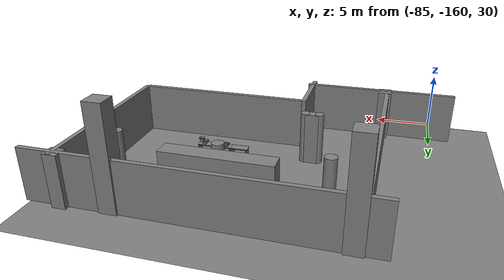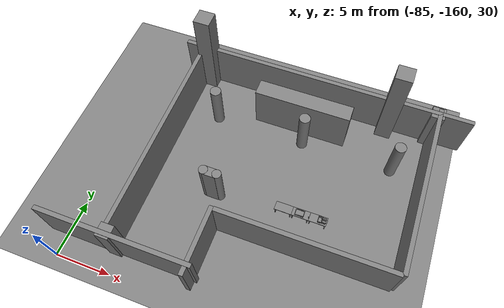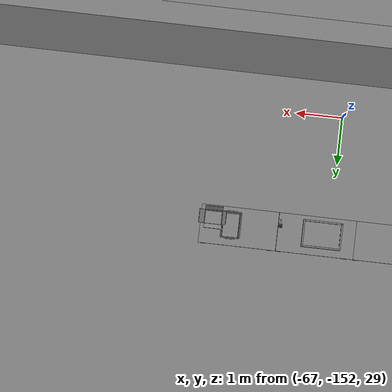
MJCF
<mujoco>
    <option gravity="0.000000000 0.000000000 -9.810000420" timestep="0.0049999999" integrator="implicitfast" density="1.225" viscosity="1.8000001e-05" noslip_iterations="10" iterations="100" sdf_iterations="50">
        <flag multiccd="disable"/>
    </option>
    <size memory="1000M"/>
    <compiler coordinate="local"/>
    <worldbody>
        <light cutoff="30" pos="0 1 1" dir="0 -1 -2"/>
        <light cutoff="30" pos="0 -1 1" dir="0 1 -2"/>
        <body pos="-64.866622925 -149.383972168 30.183746338" euler="89.999992371 89.999946594 0.000000000" name="openloong_gripper_2f85_fix_base_usda_bluebox_01">
            <geom contype="1" conaffinity="1" density="1000" type="box" material="" rgba="0.500000000 0.500000000 0.500000000 1.000000000" solimp="0.899999976 0.949999988 0.001000000" friction="1.000000000 0.005000000 0.000100000" solref="0.020000000 1.000000000" margin="0" condim="3" group="0" pos="0.276596069 0.187225342 0.000061035" quat="0.707107008 0.000077501 0.707106471 0.000077456" size="0.100000001 0.057999998 0.010000000" name="openloong_gripper_2f85_fix_base_usda_geom_22440098_3EF7_4D91_9572_A4C37FD76BBD"/>
            <geom contype="1" conaffinity="1" density="1000" type="box" material="" rgba="0.500000000 0.500000000 0.500000000 1.000000000" solimp="0.899999976 0.949999988 0.001000000" friction="1.000000000 0.005000000 0.000100000" solref="0.020000000 1.000000000" margin="0" condim="3" group="0" pos="0.000000000 0.002883911 0.000000000" quat="1.000000000 0.000000000 0.000000000 0.000000000" size="0.254000008 0.003000000 0.172000006" name="openloong_gripper_2f85_fix_base_usda_geom_84BB400C_7552_453B_8970_3CD838E1C0A1"/>
            <geom contype="1" conaffinity="1" density="1000" type="box" material="" rgba="0.500000000 0.500000000 0.500000000 1.000000000" solimp="0.899999976 0.949999988 0.001000000" friction="1.000000000 0.005000000 0.000100000" solref="0.020000000 1.000000000" margin="0" condim="3" group="0" pos="0.000015259 0.124874115 0.173477173" quat="0.999796450 0.020176515 -0.000000015 0.000000030" size="0.259999990 0.119999997 0.007000000" name="openloong_gripper_2f85_fix_base_usda_geom_38A2A451_3A7C_4D5E_BA17_C531B7E13E06"/>
            <geom contype="1" conaffinity="1" density="1000" type="box" material="" rgba="0.500000000 0.500000000 0.500000000 1.000000000" solimp="0.899999976 0.949999988 0.001000000" friction="1.000000000 0.005000000 0.000100000" solref="0.020000000 1.000000000" margin="0" condim="3" group="0" pos="0.000015259 0.124874115 -0.173477173" quat="0.999796450 -0.020176545 -0.000000015 0.000000000" size="0.259999990 0.119999997 0.007000000" name="openloong_gripper_2f85_fix_base_usda_geom_32B61AF7_AD2C_4FC6_85D1_D99D2A94C5AD"/>
            <geom contype="1" conaffinity="1" density="1000" type="box" material="" rgba="0.500000000 0.500000000 0.500000000 1.000000000" solimp="0.899999976 0.949999988 0.001000000" friction="1.000000000 0.005000000 0.000100000" solref="0.020000000 1.000000000" margin="0" condim="3" group="0" pos="0.000015259 0.214012146 0.188980103" quat="0.999913096 0.013176724 0.000000015 0.000000000" size="0.259999990 0.029999999 0.012500000" name="openloong_gripper_2f85_fix_base_usda_geom_D3110DAD_7987_4C18_934E_A20F0C7C3081"/>
            <geom contype="1" conaffinity="1" density="1000" type="box" material="" rgba="0.500000000 0.500000000 0.500000000 1.000000000" solimp="0.899999976 0.949999988 0.001000000" friction="1.000000000 0.005000000 0.000100000" solref="0.020000000 1.000000000" margin="0" condim="3" group="0" pos="-0.258346558 0.125289917 0.001876831" quat="0.702796996 -0.020792052 0.710783184 0.020769238" size="0.189999998 0.119999997 0.009000000" name="openloong_gripper_2f85_fix_base_usda_geom_0ADCA4B1_945E_4DBA_A4E6_6B871FF2E1B2"/>
            <geom contype="1" conaffinity="1" density="1000" type="box" material="" rgba="0.500000000 0.500000000 0.500000000 1.000000000" solimp="0.899999976 0.949999988 0.001000000" friction="1.000000000 0.005000000 0.000100000" solref="0.020000000 1.000000000" margin="0" condim="3" group="0" pos="0.000015259 0.214012146 -0.188980103" quat="0.999913096 -0.013176769 0.000000030 0.000000015" size="0.259999990 0.029999999 0.012500000" name="openloong_gripper_2f85_fix_base_usda_geom_2D8A280C_1A55_4BC1_99D6_18549489B864"/>
            <geom contype="1" conaffinity="1" density="1000" type="box" material="" rgba="0.500000000 0.500000000 0.500000000 1.000000000" solimp="0.899999976 0.949999988 0.001000000" friction="1.000000000 0.005000000 0.000100000" solref="0.020000000 1.000000000" margin="0" condim="3" group="0" pos="-0.276596069 0.187225342 0.000061035" quat="0.707106650 0.000077441 0.707106709 0.000077456" size="0.100000001 0.057999998 0.010000000" name="openloong_gripper_2f85_fix_base_usda_geom_71EF17F1_B712_453E_892D_DFC946E379B5"/>
            <geom contype="1" conaffinity="1" density="1000" type="box" material="" rgba="0.500000000 0.500000000 0.500000000 1.000000000" solimp="0.899999976 0.949999988 0.001000000" friction="1.000000000 0.005000000 0.000100000" solref="0.020000000 1.000000000" margin="0" condim="3" group="0" pos="0.258346558 0.125289917 0.001876831" quat="0.702851534 0.018856451 0.710823834 -0.019329429" size="0.189999998 0.119999997 0.009000000" name="openloong_gripper_2f85_fix_base_usda_geom_7FCF241E_B787_43DA_AE6C_A5993C6E903C"/>
            <freejoint name="openloong_gripper_2f85_fix_base_usda_bluebox_01_joint"/>
            <site size="0.005000000 0.005000000 0.005000000" rgba="0.500000000 0.500000000 0.500000000 1.000000000" pos="0.000000000 0.000000000 0.000000000" quat="0.999961913 0.008726534 0.000000000 0.000000000" group="0" type="sphere" name="openloong_gripper_2f85_fix_base_usda_bluebox_01site"/>
        </body>
        <body pos="-64.496299744 -149.491867065 30.235729218" euler="0.000000000 0.000000000 89.999946594" name="openloong_gripper_2f85_fix_base_usda_cardboardbox_01">
            <geom contype="1" conaffinity="1" density="1000" type="box" material="" rgba="0.500000000 0.500000000 0.500000000 1.000000000" solimp="0.899999976 0.949999988 0.001000000" friction="1.000000000 0.005000000 0.000100000" solref="0.020000000 1.000000000" margin="0" condim="3" group="0" pos="-0.003166199 -0.004086494 0.005052090" quat="1.000000000 0.000000000 0.000000000 0.000000000" size="0.142499998 0.177500010 0.005000000" name="openloong_gripper_2f85_fix_base_usda_geom_6440D5ED_7074_406A_B036_B19D8A4F727F"/>
            <geom contype="1" conaffinity="1" density="1000" type="box" material="" rgba="0.500000000 0.500000000 0.500000000 1.000000000" solimp="0.899999976 0.949999988 0.001000000" friction="1.000000000 0.005000000 0.000100000" solref="0.020000000 1.000000000" margin="0" condim="3" group="0" pos="-0.003166199 0.170316696 0.150570869" quat="1.000000000 0.000000000 0.000000000 0.000000000" size="0.142499998 0.005000000 0.149999991" name="openloong_gripper_2f85_fix_base_usda_geom_6D6D9292_3756_4799_9072_7572A8F7149D"/>
            <geom contype="1" conaffinity="1" density="1000" type="box" material="" rgba="0.500000000 0.500000000 0.500000000 1.000000000" solimp="0.899999976 0.949999988 0.001000000" friction="1.000000000 0.005000000 0.000100000" solref="0.020000000 1.000000000" margin="0" condim="3" group="0" pos="-0.147399902 -0.005307198 0.150570869" quat="1.000000000 0.000000000 0.000000000 0.000000000" size="0.005000000 0.177500010 0.149999991" name="openloong_gripper_2f85_fix_base_usda_geom_E58BD7E2_1979_412F_8EFC_7294C06960A7"/>
            <geom contype="1" conaffinity="1" density="1000" type="box" material="" rgba="0.500000000 0.500000000 0.500000000 1.000000000" solimp="0.899999976 0.949999988 0.001000000" friction="1.000000000 0.005000000 0.000100000" solref="0.020000000 1.000000000" margin="0" condim="3" group="0" pos="0.140275955 -0.005307198 0.150570869" quat="1.000000000 0.000000000 0.000000000 0.000000000" size="0.005000000 0.177500010 0.149999991" name="openloong_gripper_2f85_fix_base_usda_geom_1F7D1C46_52B3_4578_80F2_3DB6FD80031D"/>
            <geom contype="1" conaffinity="1" density="1000" type="box" material="" rgba="0.500000000 0.500000000 0.500000000 1.000000000" solimp="0.899999976 0.949999988 0.001000000" friction="1.000000000 0.005000000 0.000100000" solref="0.020000000 1.000000000" margin="0" condim="3" group="0" pos="-0.003166199 -0.181550980 0.150570869" quat="1.000000000 0.000000000 0.000000000 0.000000000" size="0.142499998 0.005000000 0.149999991" name="openloong_gripper_2f85_fix_base_usda_geom_DB942CAB_0D44_49CD_9EE2_3633FA17F02D"/>
            <freejoint name="openloong_gripper_2f85_fix_base_usda_cardboardbox_01_joint"/>
            <site size="0.005000000 0.005000000 0.005000000" rgba="0.500000000 0.500000000 0.500000000 1.000000000" pos="0.000000000 0.000000000 0.000000000" quat="0.999961913 0.008726535 0.000000000 0.000000000" group="0" type="sphere" name="openloong_gripper_2f85_fix_base_usda_site_49571598_AEA3_41C8_94A6_BEFC8FDDA60C"/>
            <body pos="0.139160156 -0.004048347 0.301930904" euler="-179.999954224 49.383502960 179.999954224" name="openloong_gripper_2f85_fix_base_usda_A1_006">
                <geom contype="1" conaffinity="1" density="1000" type="box" material="" rgba="0.500000000 0.500000000 0.500000000 1.000000000" solimp="0.899999976 0.949999988 0.001000000" friction="1.000000000 0.005000000 0.000100000" solref="0.020000000 1.000000000" margin="0" condim="3" group="0" pos="-0.071587563 0.000009537 0.001745224" quat="0.999999881 0.000000000 0.000000000 0.000000000" size="0.071249999 0.179999992 0.002500000" name="openloong_gripper_2f85_fix_base_usda_geom_70D004A9_DB5C_4326_A1D7_4FF29CC4501E"/>
                <joint armature="0" stiffness="0.07" damping="0.0099999998" axis="0.000000 1.000000 0.000000" type="hinge" name="openloong_gripper_2f85_fix_base_usda_A1_006"/>
            </body>
            <body pos="-0.145902634 -0.004086494 0.301938057" euler="-180.000000000 -60.000011444 -180.000000000" name="openloong_gripper_2f85_fix_base_usda_A2_006">
                <geom contype="1" conaffinity="1" density="1000" type="box" material="" rgba="0.500000000 0.500000000 0.500000000 1.000000000" solimp="0.899999976 0.949999988 0.001000000" friction="1.000000000 0.005000000 0.000100000" solref="0.020000000 1.000000000" margin="0" condim="3" group="0" pos="0.071268082 0.000009537 0.002717972" quat="0.000002921 0.000000000 -0.000000030 0.999999881" size="0.071249999 0.179999992 0.002500000" name="openloong_gripper_2f85_fix_base_usda_geom_656A7949_B1EA_423D_A102_D3B189197C35"/>
                <joint armature="0" stiffness="0.07" damping="0.0099999998" axis="0.000000 1.000000 0.000000" type="hinge" name="openloong_gripper_2f85_fix_base_usda_A2_006"/>
            </body>
            <body pos="-0.003385544 0.175991058 0.301930904" euler="-125.858116150 -0.000004561 0.000002331" name="openloong_gripper_2f85_fix_base_usda_B2_006">
                <geom contype="1" conaffinity="1" density="1000" type="box" material="" rgba="0.500000000 0.500000000 0.500000000 1.000000000" solimp="0.899999976 0.949999988 0.001000000" friction="1.000000000 0.005000000 0.000100000" solref="0.020000000 1.000000000" margin="0" condim="3" group="0" pos="0.000009537 -0.070939064 -0.002470016" quat="0.999614120 0.027776197 -0.000000015 0.000000030" size="0.137500003 0.064999998 0.005000000" name="openloong_gripper_2f85_fix_base_usda_geom_F9E78A75_2C30_4E87_BE6F_4BF3FBF117DD"/>
                <joint armature="0" stiffness="0.07" damping="0.0099999998" axis="1.000000 0.000000 0.000000" type="hinge" name="openloong_gripper_2f85_fix_base_usda_B2_006"/>
            </body>
            <body pos="-0.003385544 -0.184140205 0.301938057" euler="147.805557251 0.000000000 0.000000000" name="openloong_gripper_2f85_fix_base_usda_B1_006">
                <geom contype="1" conaffinity="1" density="1000" type="box" material="" rgba="0.500000000 0.500000000 0.500000000 1.000000000" solimp="0.899999976 0.949999988 0.001000000" friction="1.000000000 0.005000000 0.000100000" solref="0.020000000 1.000000000" margin="0" condim="3" group="0" pos="-0.000028610 0.070202351 -0.002703667" quat="0.999614179 -0.027776167 0.000000000 0.000000000" size="0.137500003 0.064999998 0.005000000" name="openloong_gripper_2f85_fix_base_usda_geom_B59D58F5_5A6F_4131_A83F_4D31279692CC"/>
                <joint armature="0" stiffness="0.07" damping="0.0099999998" axis="1.000000 0.000000 0.000000" type="hinge" name="openloong_gripper_2f85_fix_base_usda_B1_006"/>
            </body>
        </body>
        <body pos="-65.882858276 -149.481979370 30.229999542" euler="-64.487716675 0.000000000 0.000000000" name="openloong_gripper_2f85_fix_base_usda_Barcode">
            <geom contype="1" conaffinity="1" density="1000" type="box" material="" rgba="0.500000000 0.500000000 0.500000000 1.000000000" solimp="0.899999976 0.949999988 0.001000000" friction="1.000000000 0.005000000 0.000100000" solref="0.020000000 1.000000000" margin="0" condim="3" group="0" pos="0.000000000 0.013038635 0.001419067" quat="0.000000000 0.000000000 0.000000000 1.000000119" size="0.034000002 0.010000000 0.017999999" name="openloong_gripper_2f85_fix_base_usda_geom_98110209_1E3A_4956_89B5_B0D9FF397A6B"/>
            <geom contype="1" conaffinity="1" density="1000" type="box" material="" rgba="0.500000000 0.500000000 0.500000000 1.000000000" solimp="0.899999976 0.949999988 0.001000000" friction="1.000000000 0.005000000 0.000100000" solref="0.020000000 1.000000000" margin="0" condim="3" group="0" pos="0.000000000 -0.035301208 -0.007095337" quat="0.000000000 0.000000000 -0.043619365 0.999048233" size="0.028999999 0.010000000 0.020000000" name="openloong_gripper_2f85_fix_base_usda_geom_0CB2AFFE_EC8C_433C_BB0A_13F20A9E1272"/>
            <geom contype="1" conaffinity="1" density="1000" type="box" material="" rgba="0.500000000 0.500000000 0.500000000 1.000000000" solimp="0.899999976 0.949999988 0.001000000" friction="1.000000000 0.005000000 0.000100000" solref="0.020000000 1.000000000" margin="0" condim="3" group="0" pos="0.000000000 -0.043411255 -0.011749268" quat="0.922262907 0.386563420 0.000000000 0.000000000" size="0.026000001 0.010000000 0.020000000" name="openloong_gripper_2f85_fix_base_usda_geom_9C6D832D_2118_414D_A27B_69A04083B7F2"/>
            <geom contype="1" conaffinity="1" density="1000" type="box" material="" rgba="0.500000000 0.500000000 0.500000000 1.000000000" solimp="0.899999976 0.949999988 0.001000000" friction="1.000000000 0.005000000 0.000100000" solref="0.020000000 1.000000000" margin="0" condim="3" group="0" pos="0.000000000 -0.016967773 -0.031860352" quat="0.000000000 0.000000000 0.000000000 1.000000119" size="0.008000000 0.010000000 0.013000000" name="openloong_gripper_2f85_fix_base_usda_geom_65E3F7C3_279C_472B_A99D_8C4A2E95CC95"/>
            <geom contype="1" conaffinity="1" density="1000" type="box" material="" rgba="0.500000000 0.500000000 0.500000000 1.000000000" solimp="0.899999976 0.949999988 0.001000000" friction="1.000000000 0.005000000 0.000100000" solref="0.020000000 1.000000000" margin="0" condim="3" group="0" pos="0.000000000 -0.001869202 0.000312805" quat="0.953716993 0.300705761 0.000000000 0.000000000" size="0.032000002 0.010000000 0.018999999" name="openloong_gripper_2f85_fix_base_usda_geom_39C32BF1_5289_4B70_8DFD_060FAA5E76FA"/>
            <geom contype="1" conaffinity="1" density="1000" type="box" material="" rgba="0.500000000 0.500000000 0.500000000 1.000000000" solimp="0.899999976 0.949999988 0.001000000" friction="1.000000000 0.005000000 0.000100000" solref="0.020000000 1.000000000" margin="0" condim="3" group="0" pos="0.000000000 -0.019531250 -0.003173828" quat="0.953716993 0.300705761 0.000000000 0.000000000" size="0.030999999 0.010000000 0.020000000" name="openloong_gripper_2f85_fix_base_usda_geom_2E23B48B_A423_44A3_AB97_E39E51B0C07F"/>
            <geom contype="1" conaffinity="1" density="1000" type="box" material="" rgba="0.500000000 0.500000000 0.500000000 1.000000000" solimp="0.899999976 0.949999988 0.001000000" friction="1.000000000 0.005000000 0.000100000" solref="0.020000000 1.000000000" margin="0" condim="3" group="0" pos="0.000000000 -0.035301208 -0.007095337" quat="0.953716993 0.300705761 0.000000000 0.000000000" size="0.028999999 0.010000000 0.020000000" name="openloong_gripper_2f85_fix_base_usda_geom_0102C6B3_822B_4BB2_B58B_A48D2F7F9A17"/>
            <geom contype="1" conaffinity="1" density="1000" type="box" material="" rgba="0.500000000 0.500000000 0.500000000 1.000000000" solimp="0.899999976 0.949999988 0.001000000" friction="1.000000000 0.005000000 0.000100000" solref="0.020000000 1.000000000" margin="0" condim="3" group="0" pos="0.000000000 -0.042617798 -0.071121216" quat="0.000000000 0.000000000 0.000000000 1.000000119" size="0.013000000 0.021000000 0.059999999" name="openloong_gripper_2f85_fix_base_usda_geom_AFAC3FA3_BAAB_422B_9446_A4DB4FD8BD93"/>
            <freejoint name="openloong_gripper_2f85_fix_base_usda_Barcode_joint"/>
            <site size="0.005000000 0.005000000 0.005000000" rgba="0.500000000 0.500000000 0.500000000 1.000000000" pos="0.000000000 0.000000000 0.000000000" quat="1.000000000 0.000000000 0.000000000 0.000000000" group="0" type="sphere" name="openloong_gripper_2f85_fix_base_usda_Barcode_site"/>
        </body>
        <body pos="-66.745018005 -149.392349243 30.184000015" euler="0.000000000 0.000000000 89.999946594" name="[22330991401255]_Basket_01">
            <geom contype="1" conaffinity="1" density="1000" type="box" material="" rgba="0.500000000 0.500000000 0.500000000 1.000000000" solimp="0.899999976 0.949999988 0.001000000" friction="1.000000000 0.005000000 0.000100000" solref="0.020000000 1.000000000" margin="0" condim="3" group="0" pos="-0.052425385 0.389207840 0.089787483" quat="0.707107008 0.000000000 0.000000000 0.707106411" size="0.014249999 0.014249999 0.059999999" name="[22330991401255]_geom_86E4EFA8_BF44_463D_94DD_975D9593D012"/>
            <geom contype="1" conaffinity="1" density="1000" type="box" material="" rgba="0.500000000 0.500000000 0.500000000 1.000000000" solimp="0.899999976 0.949999988 0.001000000" friction="1.000000000 0.005000000 0.000100000" solref="0.020000000 1.000000000" margin="0" condim="3" group="0" pos="0.264015198 -0.133043289 0.089787483" quat="0.707107008 0.000000000 0.000000000 0.707106411" size="0.014249999 0.014249999 0.059999999" name="[22330991401255]_geom_ECDD9A3B_3C78_41DE_8981_125B099A3846"/>
            <geom contype="1" conaffinity="1" density="1000" type="box" material="" rgba="0.500000000 0.500000000 0.500000000 1.000000000" solimp="0.899999976 0.949999988 0.001000000" friction="1.000000000 0.005000000 0.000100000" solref="0.020000000 1.000000000" margin="0" condim="3" group="0" pos="-0.264015198 -0.265548706 0.089793205" quat="0.707107008 0.000000000 0.000000000 0.707106411" size="0.014249999 0.014249999 0.059999999" name="[22330991401255]_geom_DF5AD6B1_3DEA_4BCF_8A42_7002AC5CD0E7"/>
            <geom contype="1" conaffinity="1" density="1000" type="box" material="" rgba="0.500000000 0.500000000 0.500000000 1.000000000" solimp="0.899999976 0.949999988 0.001000000" friction="1.000000000 0.005000000 0.000100000" solref="0.020000000 1.000000000" margin="0" condim="3" group="0" pos="-0.160263062 -0.389322281 0.089793205" quat="0.707107008 0.000000000 0.000000000 0.707106411" size="0.014249999 0.014249999 0.059999999" name="[22330991401255]_geom_27907B64_DD1B_416D_86F6_403E4FC98CB0"/>
            <geom contype="1" conaffinity="1" density="1000" type="box" material="" rgba="0.500000000 0.500000000 0.500000000 1.000000000" solimp="0.899999976 0.949999988 0.001000000" friction="1.000000000 0.005000000 0.000100000" solref="0.020000000 1.000000000" margin="0" condim="3" group="0" pos="0.162265778 -0.389322281 0.089787483" quat="0.707107008 0.000000000 0.000000000 0.707106411" size="0.014249999 0.014249999 0.059999999" name="[22330991401255]_geom_67115D89_20C1_43F5_86E9_4056DB5E8294"/>
            <geom contype="1" conaffinity="1" density="1000" type="box" material="" rgba="0.500000000 0.500000000 0.500000000 1.000000000" solimp="0.899999976 0.949999988 0.001000000" friction="1.000000000 0.005000000 0.000100000" solref="0.020000000 1.000000000" margin="0" condim="3" group="0" pos="0.264015198 0.389207840 0.089787483" quat="0.707107008 0.000000000 0.000000000 0.707106411" size="0.014249999 0.014249999 0.059999999" name="[22330991401255]_geom_4B971DA7_67EE_469E_8760_63377F38A4A5"/>
            <geom contype="1" conaffinity="1" density="1000" type="box" material="" rgba="0.500000000 0.500000000 0.500000000 1.000000000" solimp="0.899999976 0.949999988 0.001000000" friction="1.000000000 0.005000000 0.000100000" solref="0.020000000 1.000000000" margin="0" condim="3" group="0" pos="-0.264015198 -0.133043289 0.089793205" quat="0.707107008 0.000000000 0.000000000 0.707106411" size="0.014249999 0.014249999 0.059999999" name="[22330991401255]_geom_ED399B36_C1B4_472D_9EC2_4DD54B17E4CF"/>
            <geom contype="1" conaffinity="1" density="1000" type="box" material="" rgba="0.500000000 0.500000000 0.500000000 1.000000000" solimp="0.899999976 0.949999988 0.001000000" friction="1.000000000 0.005000000 0.000100000" solref="0.020000000 1.000000000" margin="0" condim="3" group="0" pos="-0.264026642 0.269256592 0.089793205" quat="0.707107008 0.000000000 0.000000000 0.707106411" size="0.014249999 0.014249999 0.059999999" name="[22330991401255]_geom_578759E6_E35A_4493_8086_4180427D5C02"/>
            <geom contype="1" conaffinity="1" density="1000" type="box" material="" rgba="0.500000000 0.500000000 0.500000000 1.000000000" solimp="0.899999976 0.949999988 0.001000000" friction="1.000000000 0.005000000 0.000100000" solref="0.020000000 1.000000000" margin="0" condim="3" group="0" pos="0.054462433 0.389207840 0.089787483" quat="0.707107008 0.000000000 0.000000000 0.707106411" size="0.014249999 0.014249999 0.059999999" name="[22330991401255]_geom_9CA3B93B_0509_4E99_A588_7169663E0311"/>
            <geom contype="1" conaffinity="1" density="1000" type="box" material="" rgba="0.500000000 0.500000000 0.500000000 1.000000000" solimp="0.899999976 0.949999988 0.001000000" friction="1.000000000 0.005000000 0.000100000" solref="0.020000000 1.000000000" margin="0" condim="3" group="0" pos="0.054462433 -0.389322281 0.089787483" quat="0.707107008 0.000000000 0.000000000 0.707106411" size="0.014249999 0.014249999 0.059999999" name="[22330991401255]_geom_F433FF4A_F62C_4534_824F_8F35670C8E5B"/>
            <geom contype="1" conaffinity="1" density="1000" type="box" material="" rgba="0.500000000 0.500000000 0.500000000 1.000000000" solimp="0.899999976 0.949999988 0.001000000" friction="1.000000000 0.005000000 0.000100000" solref="0.020000000 1.000000000" margin="0" condim="3" group="0" pos="0.264015198 0.269256592 0.089793205" quat="0.707107008 0.000000000 0.000000000 0.707106411" size="0.014249999 0.014249999 0.059999999" name="[22330991401255]_geom_8C471C2C_57DE_4906_BFB7_50F3143FE9AD"/>
            <geom contype="1" conaffinity="1" density="1000" type="box" material="" rgba="0.500000000 0.500000000 0.500000000 1.000000000" solimp="0.899999976 0.949999988 0.001000000" friction="1.000000000 0.005000000 0.000100000" solref="0.020000000 1.000000000" margin="0" condim="3" group="0" pos="0.264015198 -0.389322281 0.089787483" quat="0.707107008 0.000000000 0.000000000 0.707106411" size="0.014249999 0.014249999 0.059999999" name="[22330991401255]_geom_77CF8FC0_EEBC_444D_BDBA_EE26E5BE76F4"/>
            <geom contype="1" conaffinity="1" density="1000" type="box" material="" rgba="0.500000000 0.500000000 0.500000000 1.000000000" solimp="0.899999976 0.949999988 0.001000000" friction="1.000000000 0.005000000 0.000100000" solref="0.020000000 1.000000000" margin="0" condim="3" group="0" pos="0.000000000 0.000000000 0.015998840" quat="0.707107008 0.000000000 0.000000000 0.707106411" size="0.403499991 0.279000014 0.015750000" name="[22330991401255]_geom_3CB5B816_2392_4E0B_905B_4850E3101F63"/>
            <geom contype="1" conaffinity="1" density="1000" type="box" material="" rgba="0.500000000 0.500000000 0.500000000 1.000000000" solimp="0.899999976 0.949999988 0.001000000" friction="1.000000000 0.005000000 0.000100000" solref="0.020000000 1.000000000" margin="0" condim="3" group="0" pos="0.000000000 -0.389476776 0.163619041" quat="0.707107008 0.000000000 0.000000000 0.707106411" size="0.015000000 0.277500004 0.015750000" name="[22330991401255]_geom_8EF94202_921F_4C3F_B506_3E0AD5B6DA42"/>
            <geom contype="1" conaffinity="1" density="1000" type="box" material="" rgba="0.500000000 0.500000000 0.500000000 1.000000000" solimp="0.899999976 0.949999988 0.001000000" friction="1.000000000 0.005000000 0.000100000" solref="0.020000000 1.000000000" margin="0" condim="3" group="0" pos="0.162265778 0.389207840 0.089787483" quat="0.707107008 0.000000000 0.000000000 0.707106411" size="0.014249999 0.014249999 0.059999999" name="[22330991401255]_geom_1212EDC2_67DF_4447_B56C_288CB91933F1"/>
            <geom contype="1" conaffinity="1" density="1000" type="box" material="" rgba="0.500000000 0.500000000 0.500000000 1.000000000" solimp="0.899999976 0.949999988 0.001000000" friction="1.000000000 0.005000000 0.000100000" solref="0.020000000 1.000000000" margin="0" condim="3" group="0" pos="0.000000000 0.389471054 0.163619041" quat="0.707107008 0.000000000 0.000000000 0.707106411" size="0.015000000 0.277500004 0.015750000" name="[22330991401255]_geom_78DEDDFA_D193_487D_9234_5DA2269A59E1"/>
            <geom contype="1" conaffinity="1" density="1000" type="box" material="" rgba="0.500000000 0.500000000 0.500000000 1.000000000" solimp="0.899999976 0.949999988 0.001000000" friction="1.000000000 0.005000000 0.000100000" solref="0.020000000 1.000000000" margin="0" condim="3" group="0" pos="-0.263511658 0.000000000 0.163619041" quat="0.707107008 0.000000000 0.000000000 0.707106411" size="0.403499991 0.015000000 0.015750000" name="[22330991401255]_geom_658FEB20_4191_40CF_B34B_2E9F46FF63F2"/>
            <geom contype="1" conaffinity="1" density="1000" type="box" material="" rgba="0.500000000 0.500000000 0.500000000 1.000000000" solimp="0.899999976 0.949999988 0.001000000" friction="1.000000000 0.005000000 0.000100000" solref="0.020000000 1.000000000" margin="0" condim="3" group="0" pos="-0.264015198 0.141334534 0.089793205" quat="0.707107008 0.000000000 0.000000000 0.707106411" size="0.014249999 0.014249999 0.059999999" name="[22330991401255]_geom_9F63014B_F72D_4595_BFE6_C23B494EDBF7"/>
            <geom contype="1" conaffinity="1" density="1000" type="box" material="" rgba="0.500000000 0.500000000 0.500000000 1.000000000" solimp="0.899999976 0.949999988 0.001000000" friction="1.000000000 0.005000000 0.000100000" solref="0.020000000 1.000000000" margin="0" condim="3" group="0" pos="0.264015198 -0.265548706 0.089787483" quat="0.707107008 0.000000000 0.000000000 0.707106411" size="0.014249999 0.014249999 0.059999999" name="[22330991401255]_geom_76D1EB8C_9A73_42C2_A208_A61D4746989B"/>
            <geom contype="1" conaffinity="1" density="1000" type="box" material="" rgba="0.500000000 0.500000000 0.500000000 1.000000000" solimp="0.899999976 0.949999988 0.001000000" friction="1.000000000 0.005000000 0.000100000" solref="0.020000000 1.000000000" margin="0" condim="3" group="0" pos="-0.160263062 0.389207840 0.089787483" quat="0.707107008 0.000000000 0.000000000 0.707106411" size="0.014249999 0.014249999 0.059999999" name="[22330991401255]_geom_90CF83DA_1299_4DCE_A8A5_C53D31C8C6DC"/>
            <geom contype="1" conaffinity="1" density="1000" type="box" material="" rgba="0.500000000 0.500000000 0.500000000 1.000000000" solimp="0.899999976 0.949999988 0.001000000" friction="1.000000000 0.005000000 0.000100000" solref="0.020000000 1.000000000" margin="0" condim="3" group="0" pos="-0.052425385 -0.389322281 0.089787483" quat="0.707107008 0.000000000 0.000000000 0.707106411" size="0.014249999 0.014249999 0.059999999" name="[22330991401255]_geom_07431642_E755_40D1_A59F_D8213199FA4B"/>
            <geom contype="1" conaffinity="1" density="1000" type="box" material="" rgba="0.500000000 0.500000000 0.500000000 1.000000000" solimp="0.899999976 0.949999988 0.001000000" friction="1.000000000 0.005000000 0.000100000" solref="0.020000000 1.000000000" margin="0" condim="3" group="0" pos="-0.264026642 -0.389322281 0.089793205" quat="0.707107008 0.000000000 0.000000000 0.707106411" size="0.014249999 0.014249999 0.059999999" name="[22330991401255]_geom_746917FD_23DD_47DB_9DA6_442929C44D10"/>
            <geom contype="1" conaffinity="1" density="1000" type="box" material="" rgba="0.500000000 0.500000000 0.500000000 1.000000000" solimp="0.899999976 0.949999988 0.001000000" friction="1.000000000 0.005000000 0.000100000" solref="0.020000000 1.000000000" margin="0" condim="3" group="0" pos="0.264015198 0.141334534 0.089787483" quat="0.707107008 0.000000000 0.000000000 0.707106411" size="0.014249999 0.014249999 0.059999999" name="[22330991401255]_geom_3954E38E_F0C7_4EFD_84F9_AAA762210A74"/>
            <geom contype="1" conaffinity="1" density="1000" type="box" material="" rgba="0.500000000 0.500000000 0.500000000 1.000000000" solimp="0.899999976 0.949999988 0.001000000" friction="1.000000000 0.005000000 0.000100000" solref="0.020000000 1.000000000" margin="0" condim="3" group="0" pos="-0.264015198 0.389207840 0.089793205" quat="0.707107008 0.000000000 0.000000000 0.707106411" size="0.014249999 0.014249999 0.059999999" name="[22330991401255]_geom_24FAED80_76D9_4015_B7E6_2A8825E5076C"/>
            <geom contype="1" conaffinity="1" density="1000" type="box" material="" rgba="0.500000000 0.500000000 0.500000000 1.000000000" solimp="0.899999976 0.949999988 0.001000000" friction="1.000000000 0.005000000 0.000100000" solref="0.020000000 1.000000000" margin="0" condim="3" group="0" pos="0.264015198 0.004480362 0.089787483" quat="0.707107008 0.000000000 0.000000000 0.707106411" size="0.014249999 0.014249999 0.059999999" name="[22330991401255]_geom_20B8D1E9_D548_4AF4_B4AC_CC92A72C51AD"/>
            <geom contype="1" conaffinity="1" density="1000" type="box" material="" rgba="0.500000000 0.500000000 0.500000000 1.000000000" solimp="0.899999976 0.949999988 0.001000000" friction="1.000000000 0.005000000 0.000100000" solref="0.020000000 1.000000000" margin="0" condim="3" group="0" pos="0.263694763 -0.000011444 0.163619041" quat="0.707107008 0.000000000 0.000000000 0.707106411" size="0.403499991 0.015000000 0.015750000" name="[22330991401255]_geom_1CE0A86B_3B41_4FDC_B75A_EC7E71598355"/>
            <geom contype="1" conaffinity="1" density="1000" type="box" material="" rgba="0.500000000 0.500000000 0.500000000 1.000000000" solimp="0.899999976 0.949999988 0.001000000" friction="1.000000000 0.005000000 0.000100000" solref="0.020000000 1.000000000" margin="0" condim="3" group="0" pos="-0.264015198 0.004480362 0.089793205" quat="0.707107008 0.000000000 0.000000000 0.707106411" size="0.014249999 0.014249999 0.059999999" name="[22330991401255]_geom_CECE153F_7330_4ADB_AC4A_FA63BE29697D"/>
            <freejoint name="[22330991401255]_joint_DCCE5B4D_B0E4_4EBB_9AD5_6A23EE565E99"/>
        </body>
        <body pos="0.000000000 0.000000000 0.000000000" euler="0.000000000 0.000000000 0.000000000" name="Static Objects_Static Objects">
            <geom contype="1" conaffinity="1" density="1000" type="box" material="" rgba="0.500000000 0.500000000 0.500000000 1.000000000" solimp="0.899999976 0.949999988 0.001000000" friction="1.000000000 0.005000000 0.000100000" solref="0.020000000 1.000000000" margin="0" condim="3" group="0" pos="-67.544113159 -149.365814209 29.727830887" quat="0.500000417 0.499999970 0.499999553 0.499999970" size="0.381000012 0.319999993 0.041000001" name="Static Objects_geom_B5A17B30_5073_4746_8F03_07F18D033CE9"/>
            <geom contype="1" conaffinity="1" density="1000" type="box" material="" rgba="0.500000000 0.500000000 0.500000000 1.000000000" solimp="0.899999976 0.949999988 0.001000000" friction="1.000000000 0.005000000 0.000100000" solref="0.020000000 1.000000000" margin="0" condim="3" group="0" pos="-68.239501953 -149.365814209 30.086868286" quat="0.500000417 0.499999970 0.499999553 0.499999970" size="0.370999992 0.039500002 0.745000005" name="Static Objects_geom_7D09CACE_F485_44B1_93CD_D976109E1738"/>
            <geom contype="1" conaffinity="1" density="1000" type="box" material="" rgba="0.500000000 0.500000000 0.500000000 1.000000000" solimp="0.899999976 0.949999988 0.001000000" friction="1.000000000 0.005000000 0.000100000" solref="0.020000000 1.000000000" margin="0" condim="3" group="0" pos="-68.239501953 -149.365814209 30.147235870" quat="0.500000417 0.499999970 0.499999553 0.499999970" size="0.400000006 0.022000000 0.800000012" name="Static Objects_geom_0F6ED2BA_A6B2_42AC_83EE_4E58EEB6A8B1"/>
            <geom contype="1" conaffinity="1" density="1000" type="box" material="" rgba="0.500000000 0.500000000 0.500000000 1.000000000" solimp="0.899999976 0.949999988 0.001000000" friction="1.000000000 0.005000000 0.000100000" solref="0.020000000 1.000000000" margin="0" condim="3" group="0" pos="-68.934890747 -149.365814209 29.727830887" quat="0.500000417 0.499999970 0.499999553 0.499999970" size="0.381000012 0.319999993 0.041000001" name="Static Objects_geom_6C3C654F_BDDF_4735_ABEC_A240CD07FBB9"/>
            <geom contype="1" conaffinity="1" density="1000" type="box" material="" rgba="0.500000000 0.500000000 0.500000000 1.000000000" solimp="0.899999976 0.949999988 0.001000000" friction="1.000000000 0.005000000 0.000100000" solref="0.020000000 1.000000000" margin="0" condim="3" group="0" pos="-68.239501953 -149.365814209 29.561563492" quat="0.500000417 0.499999970 0.499999553 0.499999970" size="0.020000000 0.022000000 0.660000026" name="Static Objects_geom_128E0C22_E057_4861_9377_ECCEA78401E9"/>
            <geom contype="1" conaffinity="1" density="1000" type="box" material="" rgba="0.500000000 0.500000000 0.500000000 1.000000000" solimp="0.899999976 0.949999988 0.001000000" friction="1.000000000 0.005000000 0.000100000" solref="0.020000000 1.000000000" margin="0" condim="3" group="0" pos="-65.945671082 -149.365814209 29.727830887" quat="0.500000417 0.499999970 0.499999553 0.499999970" size="0.381000012 0.319999993 0.041000001" name="Static Objects_geom_DD328FD4_1097_4B1C_96C5_2780ED087254"/>
            <geom contype="1" conaffinity="1" density="1000" type="box" material="" rgba="0.500000000 0.500000000 0.500000000 1.000000000" solimp="0.899999976 0.949999988 0.001000000" friction="1.000000000 0.005000000 0.000100000" solref="0.020000000 1.000000000" margin="0" condim="3" group="0" pos="-66.641059875 -149.365814209 30.086868286" quat="0.500000417 0.499999970 0.499999553 0.499999970" size="0.370999992 0.039500002 0.745000005" name="Static Objects_geom_EC8B67F4_2A0E_4C4C_8E0D_E990671CF07A"/>
            <geom contype="1" conaffinity="1" density="1000" type="box" material="" rgba="0.500000000 0.500000000 0.500000000 1.000000000" solimp="0.899999976 0.949999988 0.001000000" friction="1.000000000 0.005000000 0.000100000" solref="0.020000000 1.000000000" margin="0" condim="3" group="0" pos="-66.641059875 -149.365814209 30.147235870" quat="0.500000417 0.499999970 0.499999553 0.499999970" size="0.400000006 0.022000000 0.800000012" name="Static Objects_geom_94B87D3A_2B00_4656_99F0_BC9614DFE88E"/>
            <geom contype="1" conaffinity="1" density="1000" type="box" material="" rgba="0.500000000 0.500000000 0.500000000 1.000000000" solimp="0.899999976 0.949999988 0.001000000" friction="1.000000000 0.005000000 0.000100000" solref="0.020000000 1.000000000" margin="0" condim="3" group="0" pos="-67.336448669 -149.365814209 29.727830887" quat="0.500000417 0.499999970 0.499999553 0.499999970" size="0.381000012 0.319999993 0.041000001" name="Static Objects_geom_D522FA5F_9D26_4FE8_B53D_C7691508B6CB"/>
            <geom contype="1" conaffinity="1" density="1000" type="box" material="" rgba="0.500000000 0.500000000 0.500000000 1.000000000" solimp="0.899999976 0.949999988 0.001000000" friction="1.000000000 0.005000000 0.000100000" solref="0.020000000 1.000000000" margin="0" condim="3" group="0" pos="-66.641059875 -149.365814209 29.561563492" quat="0.500000417 0.499999970 0.499999553 0.499999970" size="0.020000000 0.022000000 0.660000026" name="Static Objects_geom_4E94872E_4E8F_47CB_8FC1_15B13C7C770E"/>
            <geom contype="1" conaffinity="1" density="1000" type="box" material="" rgba="0.500000000 0.500000000 0.500000000 1.000000000" solimp="0.899999976 0.949999988 0.001000000" friction="1.000000000 0.005000000 0.000100000" solref="0.020000000 1.000000000" margin="0" condim="3" group="0" pos="-64.338577271 -149.365814209 29.727830887" quat="0.500000417 0.499999970 0.499999553 0.499999970" size="0.381000012 0.319999993 0.041000001" name="Static Objects_geom_B344499E_1838_40F9_B57B_CF8A12E5E661"/>
            <geom contype="1" conaffinity="1" density="1000" type="box" material="" rgba="0.500000000 0.500000000 0.500000000 1.000000000" solimp="0.899999976 0.949999988 0.001000000" friction="1.000000000 0.005000000 0.000100000" solref="0.020000000 1.000000000" margin="0" condim="3" group="0" pos="-65.033966064 -149.365814209 30.086868286" quat="0.500000417 0.499999970 0.499999553 0.499999970" size="0.370999992 0.039500002 0.745000005" name="Static Objects_geom_652ABA93_F075_4D08_9BD1_5C25C5DA7FD9"/>
            <geom contype="1" conaffinity="1" density="1000" type="box" material="" rgba="0.500000000 0.500000000 0.500000000 1.000000000" solimp="0.899999976 0.949999988 0.001000000" friction="1.000000000 0.005000000 0.000100000" solref="0.020000000 1.000000000" margin="0" condim="3" group="0" pos="-65.033966064 -149.365814209 30.147235870" quat="0.500000417 0.499999970 0.499999553 0.499999970" size="0.400000006 0.022000000 0.800000012" name="Static Objects_geom_733DF5D5_0A20_41D3_8A95_3E95DD47854A"/>
            <geom contype="1" conaffinity="1" density="1000" type="box" material="" rgba="0.500000000 0.500000000 0.500000000 1.000000000" solimp="0.899999976 0.949999988 0.001000000" friction="1.000000000 0.005000000 0.000100000" solref="0.020000000 1.000000000" margin="0" condim="3" group="0" pos="-65.729354858 -149.365814209 29.727830887" quat="0.500000417 0.499999970 0.499999553 0.499999970" size="0.381000012 0.319999993 0.041000001" name="Static Objects_geom_0413B415_7DE2_4F2D_8C84_6B51A246258F"/>
            <geom contype="1" conaffinity="1" density="1000" type="box" material="" rgba="0.500000000 0.500000000 0.500000000 1.000000000" solimp="0.899999976 0.949999988 0.001000000" friction="1.000000000 0.005000000 0.000100000" solref="0.020000000 1.000000000" margin="0" condim="3" group="0" pos="-65.033966064 -149.365814209 29.561563492" quat="0.500000417 0.499999970 0.499999553 0.499999970" size="0.020000000 0.022000000 0.660000026" name="Static Objects_geom_531562CC_798B_49CC_8602_E85AEF752D08"/>
            <geom contype="1" conaffinity="1" density="1000" type="box" material="" rgba="0.500000000 0.500000000 0.500000000 1.000000000" solimp="0.899999976 0.949999988 0.001000000" friction="1.000000000 0.005000000 0.000100000" solref="0.020000000 1.000000000" margin="0" condim="3" group="0" pos="-61.754566193 -137.853729248 33.906845093" quat="0.707107067 0.000000000 0.000000000 0.707106471" size="0.759999990 0.759999990 4.500000000" name="Static Objects_geom_99F62EB3_25C8_4D51_B5DF_447B93EE3DFB"/>
            <geom contype="1" conaffinity="1" density="1000" type="box" material="" rgba="0.500000000 0.500000000 0.500000000 1.000000000" solimp="0.899999976 0.949999988 0.001000000" friction="1.000000000 0.005000000 0.000100000" solref="0.020000000 1.000000000" margin="0" condim="3" group="0" pos="-57.511135101 -144.927108765 31.707921982" quat="1.000000000 0.000000000 0.000000000 0.000000000" size="0.200000003 8.000000000 2.299999952" name="Static Objects_geom_EA503335_25B1_4774_ABD2_F12CD7751F3D"/>
            <geom contype="1" conaffinity="1" density="1000" type="box" material="" rgba="0.500000000 0.500000000 0.500000000 1.000000000" solimp="0.899999976 0.949999988 0.001000000" friction="1.000000000 0.005000000 0.000100000" solref="0.020000000 1.000000000" margin="0" condim="3" group="0" pos="-80.517646790 -157.574050903 31.688196182" quat="0.707107067 0.000000000 0.000000000 0.707106471" size="0.600000024 0.600000024 2.299999952" name="Static Objects_geom_F6EA18FA_D47A_423F_AF57_738ACBAF7069"/>
            <geom contype="1" conaffinity="1" density="1000" type="box" material="" rgba="0.500000000 0.500000000 0.500000000 1.000000000" solimp="0.899999976 0.949999988 0.001000000" friction="1.000000000 0.005000000 0.000100000" solref="0.020000000 1.000000000" margin="0" condim="3" group="0" pos="-80.711044312 -147.414932251 31.666158676" quat="1.000000000 0.000000000 0.000000000 0.000000000" size="0.200000003 10.000000000 2.299999952" name="Static Objects_geom_1EBCEED0_5820_4F94_A546_7F9B23C67538"/>
            <geom contype="1" conaffinity="1" density="1000" type="box" material="" rgba="0.500000000 0.500000000 0.500000000 1.000000000" solimp="0.899999976 0.949999988 0.001000000" friction="1.000000000 0.005000000 0.000100000" solref="0.020000000 1.000000000" margin="0" condim="3" group="0" pos="-57.687217712 -137.434692383 31.688196182" quat="0.707107067 0.000000000 0.000000000 0.707106471" size="0.600000024 0.600000024 2.299999952" name="Static Objects_geom_8B7BBB19_DA33_439A_B36A_DEF3B6F3D285"/>
            <geom contype="1" conaffinity="1" density="1000" type="box" material="" rgba="0.500000000 0.500000000 0.500000000 1.000000000" solimp="0.899999976 0.949999988 0.001000000" friction="1.000000000 0.005000000 0.000100000" solref="0.020000000 1.000000000" margin="0" condim="3" group="0" pos="-69.537033081 -140.263229370 31.714921951" quat="0.707107067 0.000000000 0.000000000 0.707106471" size="0.759999990 4.500000000 2.299999952" name="Static Objects_geom_1369DDBB_EC41_4BDF_A188_B35C68E26D17"/>
            <geom contype="1" conaffinity="1" density="1000" type="box" material="" rgba="0.500000000 0.500000000 0.500000000 1.000000000" solimp="0.899999976 0.949999988 0.001000000" friction="1.000000000 0.005000000 0.000100000" solref="0.020000000 1.000000000" margin="0" condim="3" group="0" pos="-80.073638916 -137.853713989 33.906845093" quat="0.707107067 0.000000000 0.000000000 0.707106471" size="0.759999990 0.759999990 4.500000000" name="Static Objects_geom_FD29175F_8214_4F60_8A72_217B8299C40A"/>
            <geom contype="1" conaffinity="1" density="1000" type="box" material="" rgba="0.500000000 0.500000000 0.500000000 1.000000000" solimp="0.899999976 0.949999988 0.001000000" friction="1.000000000 0.005000000 0.000100000" solref="0.020000000 1.000000000" margin="0" condim="3" group="0" pos="-73.406707764 -155.734664917 31.707921982" quat="1.000000000 0.000000000 0.000000000 0.000000000" size="0.200000003 3.000000000 2.299999952" name="Static Objects_geom_E9146CB0_AA3D_441A_8055_3F3C20F48A3A"/>
            <geom contype="1" conaffinity="1" density="1000" type="box" material="" rgba="0.500000000 0.500000000 0.500000000 1.000000000" solimp="0.899999976 0.949999988 0.001000000" friction="1.000000000 0.005000000 0.000100000" solref="0.020000000 1.000000000" margin="0" condim="3" group="0" pos="-68.497543335 -137.448257446 31.707921982" quat="0.707107067 0.000000000 0.000000000 0.707106471" size="0.200000003 14.000000000 2.299999952" name="Static Objects_geom_873CACFE_54A4_4B72_81F8_12DA2731191A"/>
            <geom contype="1" conaffinity="1" density="1000" type="cylinder" material="" rgba="0.500000000 0.500000000 0.500000000 1.000000000" solimp="0.899999976 0.949999988 0.001000000" friction="1.000000000 0.005000000 0.000100000" solref="0.020000000 1.000000000" margin="0" condim="3" group="0" pos="-68.868522644 -142.134506226 31.711090088" quat="0.707107067 0.000000000 0.000000000 0.707106471" size="0.509999990 2.299999952 1.000000000" name="Static Objects_geom_AFD4116C_8C9E_4143_A4FF_C56ECB6EB8D1"/>
            <geom contype="1" conaffinity="1" density="1000" type="plane" material="" rgba="0.500000000 0.500000000 0.500000000 1.000000000" solimp="0.899999976 0.949999988 0.001000000" friction="1.000000000 0.005000000 0.000100000" solref="0.020000000 1.000000000" margin="0" condim="3" group="0" pos="-72.873703003 -147.131927490 29.409669876" quat="1.000000000 0.000000000 0.000000000 0.000000000" size="18.000000000 14.000000000 1.000000000" name="Static Objects_geom_CC39B7AC_5D15_46FF_8C68_F50A59A63E30"/>
            <geom contype="1" conaffinity="1" density="1000" type="box" material="" rgba="0.500000000 0.500000000 0.500000000 1.000000000" solimp="0.899999976 0.949999988 0.001000000" friction="1.000000000 0.005000000 0.000100000" solref="0.020000000 1.000000000" margin="0" condim="3" group="0" pos="-79.943580627 -157.782272339 31.707921982" quat="0.707107067 0.000000000 0.000000000 0.707106471" size="0.200000003 7.000000000 2.299999952" name="Static Objects_geom_72A1EB2D_23B5_4F51_B13C_A4DBBED90E34"/>
            <geom contype="1" conaffinity="1" density="1000" type="box" material="" rgba="0.500000000 0.500000000 0.500000000 1.000000000" solimp="0.899999976 0.949999988 0.001000000" friction="1.000000000 0.005000000 0.000100000" solref="0.020000000 1.000000000" margin="0" condim="3" group="0" pos="-65.421028137 -152.903442383 31.707921982" quat="0.707107067 0.000000000 0.000000000 0.707106471" size="0.200000003 7.800000191 2.299999952" name="Static Objects_geom_0107CCD4_9B04_48CE_AD83_F248AA32E334"/>
            <geom contype="1" conaffinity="1" density="1000" type="box" material="" rgba="0.500000000 0.500000000 0.500000000 1.000000000" solimp="0.899999976 0.949999988 0.001000000" friction="1.000000000 0.005000000 0.000100000" solref="0.020000000 1.000000000" margin="0" condim="3" group="0" pos="-74.776908875 -149.964416504 31.688196182" quat="1.000000000 0.000000000 0.000000000 0.000000000" size="0.600000024 0.409999996 2.299999952" name="Static Objects_geom_6A578787_9DC4_48A8_89AB_2FA28DFB615D"/>
            <geom contype="1" conaffinity="1" density="1000" type="cylinder" material="" rgba="0.500000000 0.500000000 0.500000000 1.000000000" solimp="0.899999976 0.949999988 0.001000000" friction="1.000000000 0.005000000 0.000100000" solref="0.020000000 1.000000000" margin="0" condim="3" group="0" pos="-60.161884308 -142.134506226 31.711090088" quat="0.707107067 0.000000000 0.000000000 0.707106471" size="0.509999990 2.299999952 1.000000000" name="Static Objects_geom_78E9B1AD_F077_4389_B9E0_A2ED45727080"/>
            <geom contype="1" conaffinity="1" density="1000" type="cylinder" material="" rgba="0.500000000 0.500000000 0.500000000 1.000000000" solimp="0.899999976 0.949999988 0.001000000" friction="1.000000000 0.005000000 0.000100000" solref="0.020000000 1.000000000" margin="0" condim="3" group="0" pos="-75.382453918 -149.963455200 31.711090088" quat="0.707107067 0.000000000 0.000000000 0.707106471" size="0.409999996 2.299999952 1.000000000" name="Static Objects_geom_41A6D88E_1E4B_4867_AD89_9A51D02E4008"/>
            <geom contype="1" conaffinity="1" density="1000" type="cylinder" material="" rgba="0.500000000 0.500000000 0.500000000 1.000000000" solimp="0.899999976 0.949999988 0.001000000" friction="1.000000000 0.005000000 0.000100000" solref="0.020000000 1.000000000" margin="0" condim="3" group="0" pos="-74.154960632 -149.963455200 31.711090088" quat="0.707107067 0.000000000 0.000000000 0.707106471" size="0.409999996 2.299999952 1.000000000" name="Static Objects_geom_618AD50C_A1A1_4E5A_A112_D93DAB867758"/>
            <geom contype="1" conaffinity="1" density="1000" type="cylinder" material="" rgba="0.500000000 0.500000000 0.500000000 1.000000000" solimp="0.899999976 0.949999988 0.001000000" friction="1.000000000 0.005000000 0.000100000" solref="0.020000000 1.000000000" margin="0" condim="3" group="0" pos="-77.566612244 -142.134506226 31.711090088" quat="0.707107067 0.000000000 0.000000000 0.707106471" size="0.509999990 2.299999952 1.000000000" name="Static Objects_geom_676B8523_F361_4D4B_9C35_282EAA4C28A3"/>
        </body>
        <body pos="-66.291030884 -149.869689941 29.018842697" euler="0.000000000 0.000000000 89.999946594" mocap="true" name="openloong_gripper_2f85_fix_base_usda_leftHandMocap"/>
        <body pos="-66.291030884 -149.869689941 29.018842697" euler="0.000000000 0.000000000 89.999946594" mocap="true" name="openloong_gripper_2f85_fix_base_usda_rightHandMocap"/>
        <body pos="-66.291030884 -149.869689941 30.218843460" euler="0.000000000 0.000000000 89.999946594" name="openloong_gripper_2f85_fix_base_usda_base_link">
            <geom contype="1" conaffinity="1" density="1000" type="mesh" material="" rgba="0.783999979 0.783999979 0.783999979 1.000000000" solimp="0.899999976 0.949999988 0.001000000" friction="1.000000000 0.005000000 0.000100000" solref="0.020000000 1.000000000" margin="0" condim="3" group="3" mesh="base_link" pos="0.000000000 0.000000000 0.000000000" quat="1.000000000 0.000000000 0.000000000 0.000000000" size="1.000000000 1.000000000 1.000000000" name="openloong_gripper_2f85_fix_base_usda__geom_7_A9642FD4_C420_4854_BF01_8119D2A50362"/>
            <site size="0.005000000 0.005000000 0.005000000" rgba="0.500000000 0.500000000 0.500000000 1.000000000" pos="0.000000000 0.000000000 0.000000000" quat="1.000000000 0.000000000 0.000000000 0.000000000" group="0" type="sphere" name="openloong_gripper_2f85_fix_base_usda_imu"/>
            <inertial mass="22.447001" pos="-0.005664100 -0.001336700 0.238289997" diaginertia="0.374352545 0.277180195 0.220617250" quat="0.999247074 0.035235517 -0.015086859 0.006023135"/>
            <body pos="0.000000000 0.000000000 0.299997330" euler="0.000000000 0.000000000 0.000000000" name="openloong_gripper_2f85_fix_base_usda_dummy_body">
                <geom contype="1" conaffinity="1" density="1000" type="sphere" material="" rgba="0.783999979 0.783999979 0.783999979 1.000000000" solimp="0.899999976 0.949999988 0.001000000" friction="1.000000000 0.005000000 0.000100000" solref="0.020000000 1.000000000" margin="0" condim="3" group="3" pos="0.000000000 0.000000000 0.000000000" quat="1.000000000 0.000000000 0.000000000 0.000000000" size="0.010000000 0.000000000 0.000000000" name="openloong_gripper_2f85_fix_base_usda__geom_8_CB77218F_29F9_418D_A765_04A51278BA16"/>
                <joint armature="0.0099999998" stiffness="0" damping="0.1" axis="0.000000 0.000000 1.000000" type="hinge" name="openloong_gripper_2f85_fix_base_usda_dummy_joint"/>
                <site size="0.010000000 0.005000000 0.005000000" rgba="0.500000000 0.500000000 0.500000000 1.000000000" pos="0.000000000 0.000000000 0.000000000" quat="1.000000000 0.000000000 0.000000000 0.000000000" group="3" type="sphere" name="openloong_gripper_2f85_fix_base_usda_dummy_site"/>
            </body>
            <body pos="0.009002686 0.000000000 0.406400681" euler="0.000000000 0.000000000 0.000000000" name="openloong_gripper_2f85_fix_base_usda_Link_head_yaw">
                <geom contype="1" conaffinity="1" density="1000" type="mesh" material="" rgba="0.783999979 0.783999979 0.783999979 1.000000000" solimp="0.899999976 0.949999988 0.001000000" friction="1.000000000 0.005000000 0.000100000" solref="0.020000000 1.000000000" margin="0" condim="3" group="3" mesh="Link_head_yaw" pos="0.000000000 0.000000000 0.000000000" quat="1.000000000 0.000000000 0.000000000 0.000000000" size="1.000000000 1.000000000 1.000000000" name="openloong_gripper_2f85_fix_base_usda__geom_10_D0B5D1B5_4BFB_4E19_85D2_B5129A0E0AF0"/>
                <inertial mass="0.84249002" pos="0.000000000 -0.002081400 0.044801001" diaginertia="0.000700588 0.000629000 0.000553812" quat="0.706933022 -0.015675601 0.015677100 0.706933022"/>
                <body pos="0.000000000 -0.034599304 0.048500061" euler="0.000000000 0.000000000 0.000000000" name="openloong_gripper_2f85_fix_base_usda_Link_head_pitch">
                    <geom contype="1" conaffinity="1" density="1000" type="mesh" material="" rgba="0.783999979 0.783999979 0.783999979 1.000000000" solimp="0.899999976 0.949999988 0.001000000" friction="1.000000000 0.005000000 0.000100000" solref="0.020000000 1.000000000" margin="0" condim="3" group="3" mesh="Link_head_pitch" pos="0.000000000 0.000000000 0.000000000" quat="1.000000000 0.000000000 0.000000000 0.000000000" size="1.000000000 1.000000000 1.000000000" name="openloong_gripper_2f85_fix_base_usda__geom_12_0808DB50_3265_486B_B3B3_0DAB39744FF8"/>
                    <inertial mass="1.3943" pos="0.020569000 0.033004001 0.125000000" diaginertia="0.006381400 0.006289940 0.004481460" quat="0.973390222 0.008406822 0.228157058 0.019624906"/>
                    <body pos="0.000000000 0.029998779 0.000000000" euler="0.000000000 0.000000000 0.000000000" name="openloong_gripper_2f85_fix_base_usda_neck_center_body">
                        <site size="0.010000000 0.005000000 0.005000000" rgba="0.500000000 0.500000000 0.500000000 1.000000000" pos="0.000000000 0.000000000 0.000000000" quat="1.000000000 0.000000000 0.000000000 0.000000000" group="3" type="sphere" name="openloong_gripper_2f85_fix_base_usda_neck_center_site"/>
                        <body pos="0.020004272 0.000000000 0.149999619" euler="-0.000002229 39.998176575 -90.000205994" name="openloong_gripper_2f85_fix_base_usda_camera_head">
                            <site size="0.010000000 0.005000000 0.005000000" rgba="0.500000000 0.500000000 0.500000000 1.000000000" pos="0.000000000 0.000000000 0.000000000" quat="1.000000000 0.000000000 0.000000000 0.000000000" group="3" type="sphere" name="openloong_gripper_2f85_fix_base_usda_camera_head_site"/>
                        </body>
                    </body>
                </body>
            </body>
            <body pos="0.003997803 -0.161598206 0.392200470" euler="0.000000000 0.000000000 0.000000000" name="openloong_gripper_2f85_fix_base_usda_Link_arm_r_01">
                <geom contype="1" conaffinity="1" density="1000" type="mesh" material="" rgba="0.783999979 0.783999979 0.783999979 1.000000000" solimp="0.899999976 0.949999988 0.001000000" friction="1.000000000 0.005000000 0.000100000" solref="0.020000000 1.000000000" margin="0" condim="3" group="3" mesh="Link_arm_r_01" pos="0.000000000 0.000000000 0.000000000" quat="1.000000000 0.000000000 0.000000000 0.000000000" size="1.000000000 1.000000000 1.000000000" name="openloong_gripper_2f85_fix_base_usda__geom_14_CC020216_74AF_4049_900F_EC34F0239DDF"/>
                <joint armature="0.0099999998" stiffness="0" damping="1" axis="0.000000 -1.000000 0.000000" limited="true" range="-170.000015259 170.000015259" type="hinge" name="openloong_gripper_2f85_fix_base_usda_J_arm_r_01"/>
                <inertial mass="0.75641" pos="0.004494600 -0.038293999 -0.000001874" diaginertia="0.000842990 0.000803050 0.000587120" quat="-0.000163502 0.707098067 0.000812463 0.707115054"/>
                <body pos="-0.041992188 -0.041000366 0.000000000" euler="0.000000000 0.000000000 0.000000000" name="openloong_gripper_2f85_fix_base_usda_Link_arm_r_02">
                    <geom contype="1" conaffinity="1" density="1000" type="mesh" material="" rgba="0.783999979 0.783999979 0.783999979 1.000000000" solimp="0.899999976 0.949999988 0.001000000" friction="1.000000000 0.005000000 0.000100000" solref="0.020000000 1.000000000" margin="0" condim="3" group="3" mesh="Link_arm_r_02" pos="0.000000000 0.000000000 0.000000000" quat="1.000000000 0.000000000 0.000000000 0.000000000" size="1.000000000 1.000000000 1.000000000" name="openloong_gripper_2f85_fix_base_usda__geom_16_6DDEA6E2_80BD_4C89_B4D2_C1B28F9CF251"/>
                    <joint armature="0.0099999998" stiffness="0" damping="1" axis="-1.000000 0.000000 0.000000" limited="true" range="-105.000244141 105.000244141" type="hinge" name="openloong_gripper_2f85_fix_base_usda_J_arm_r_02"/>
                    <inertial mass="0.98500001" pos="0.041999999 -0.067430697 0.000000000" diaginertia="0.002262690 0.001730990 0.001154020" quat="0.500000000 0.500000000 -0.500000000 0.500000000"/>
                    <body pos="0.041992188 -0.122596741 0.000000000" euler="0.000000000 0.000000000 0.000000000" name="openloong_gripper_2f85_fix_base_usda_Link_arm_r_03">
                        <geom contype="1" conaffinity="1" density="1000" type="mesh" material="" rgba="0.783999979 0.783999979 0.783999979 1.000000000" solimp="0.899999976 0.949999988 0.001000000" friction="1.000000000 0.005000000 0.000100000" solref="0.020000000 1.000000000" margin="0" condim="3" group="3" mesh="Link_arm_r_03" pos="0.000000000 0.000000000 0.000000000" quat="1.000000000 0.000000000 0.000000000 0.000000000" size="1.000000000 1.000000000 1.000000000" name="openloong_gripper_2f85_fix_base_usda__geom_18_B68B6394_5825_4DB8_9857_26567B0CD9CD"/>
                        <joint armature="0.0099999998" stiffness="0" damping="1" axis="0.000000 -1.000000 0.000000" limited="true" range="-170.000015259 170.000015259" type="hinge" name="openloong_gripper_2f85_fix_base_usda_J_arm_r_03"/>
                        <inertial mass="0.95899999" pos="-0.001413580 -0.164663002 0.020757901" diaginertia="0.002101340 0.002064590 0.000754802" quat="0.560480952 0.454391927 -0.443732947 0.531497955"/>
                        <body pos="0.035293579 -0.177406311 0.023998260" euler="0.000000000 0.000000000 0.000000000" name="openloong_gripper_2f85_fix_base_usda_Link_arm_r_04">
                            <geom contype="1" conaffinity="1" density="1000" type="mesh" material="" rgba="0.783999979 0.783999979 0.783999979 1.000000000" solimp="0.899999976 0.949999988 0.001000000" friction="1.000000000 0.005000000 0.000100000" solref="0.020000000 1.000000000" margin="0" condim="3" group="3" mesh="Link_arm_r_04" pos="0.000000000 0.000000000 0.000000000" quat="1.000000000 0.000000000 0.000000000 0.000000000" size="1.000000000 1.000000000 1.000000000" name="openloong_gripper_2f85_fix_base_usda__geom_20_517EAD1B_F798_4453_9995_524CC5542300"/>
                            <joint armature="0.0099999998" stiffness="0" damping="1" axis="-1.000000 0.000000 0.000000" limited="true" range="0.000000000 170.000015259" type="hinge" name="openloong_gripper_2f85_fix_base_usda_J_arm_r_04"/>
                            <inertial mass="0.60000002" pos="-0.038727000 -0.060766999 -0.021003000" diaginertia="0.001092610 0.000712422 0.000645102" quat="0.327701002 0.632602990 -0.467366993 0.523443997"/>
                            <body pos="-0.035293579 -0.103492737 -0.023998260" euler="0.000000000 0.000000000 0.000000000" name="openloong_gripper_2f85_fix_base_usda_Link_arm_r_05">
                                <geom contype="1" conaffinity="1" density="1000" type="mesh" material="" rgba="0.783999979 0.783999979 0.783999979 1.000000000" solimp="0.899999976 0.949999988 0.001000000" friction="1.000000000 0.005000000 0.000100000" solref="0.020000000 1.000000000" margin="0" condim="3" group="3" mesh="Link_arm_r_05" pos="0.000000000 0.000000000 0.000000000" quat="1.000000000 0.000000000 0.000000000 0.000000000" size="1.000000000 1.000000000 1.000000000" name="openloong_gripper_2f85_fix_base_usda__geom_22_30035CB3_1839_41AF_A954_AC328B9B8407"/>
                                <joint armature="0.0099999998" stiffness="0" damping="1" axis="0.000000 -1.000000 0.000000" limited="true" range="-170.000015259 170.000015259" type="hinge" name="openloong_gripper_2f85_fix_base_usda_J_arm_r_05"/>
                                <inertial mass="0.68976003" pos="0.000032712 -0.068658002 -0.000111780" diaginertia="0.002522510 0.002411100 0.000448695" quat="0.707660973 0.706543028 -0.002603360 0.002470550"/>
                                <body pos="-0.026489258 -0.196502686 0.000000000" euler="0.000000000 0.000000000 0.000000000" name="openloong_gripper_2f85_fix_base_usda_Link_arm_r_06">
                                    <geom contype="1" conaffinity="1" density="1000" type="mesh" material="" rgba="0.783999979 0.783999979 0.783999979 1.000000000" solimp="0.899999976 0.949999988 0.001000000" friction="1.000000000 0.005000000 0.000100000" solref="0.020000000 1.000000000" margin="0" condim="3" group="3" mesh="Link_arm_r_06" pos="0.000000000 0.000000000 0.000000000" quat="1.000000000 0.000000000 0.000000000 0.000000000" size="1.000000000 1.000000000 1.000000000" name="openloong_gripper_2f85_fix_base_usda__geom_24_400694DE_5A5E_4EA6_840A_3B7CB01A3738"/>
                                    <joint armature="0.0099999998" stiffness="0" damping="1" axis="1.000000 0.000000 0.000000" limited="true" range="-105.000244141 105.000244141" type="hinge" name="openloong_gripper_2f85_fix_base_usda_J_arm_r_06"/>
                                    <inertial mass="0.28" pos="0.026078001 -0.000000896 0.001663700" diaginertia="0.000156930 0.000145601 0.000104979" quat="0.707080841 0.001851080 0.001883810 0.707127810"/>
                                    <body pos="0.026489258 0.000000000 0.031799316" euler="0.000000000 0.000000000 0.000000000" name="openloong_gripper_2f85_fix_base_usda_Link_arm_r_07">
                                        <geom contype="1" conaffinity="1" density="1000" type="mesh" material="" rgba="0.783999979 0.783999979 0.783999979 1.000000000" solimp="0.899999976 0.949999988 0.001000000" friction="1.000000000 0.005000000 0.000100000" solref="0.020000000 1.000000000" margin="0" condim="3" group="3" mesh="Link_arm_r_07" pos="0.000000000 0.000000000 0.000000000" quat="1.000000000 0.000000000 0.000000000 0.000000000" size="1.000000000 1.000000000 1.000000000" name="openloong_gripper_2f85_fix_base_usda__geom_26_543D14BF_1382_43CE_8410_7A4CD392B623"/>
                                        <joint armature="0.0099999998" stiffness="0" damping="1" axis="0.000000 0.000000 1.000000" limited="true" range="-60.000133514 60.000133514" type="hinge" name="openloong_gripper_2f85_fix_base_usda_J_arm_r_07"/>
                                        <inertial mass="0.61353999" pos="-0.007859000 -0.158170000 -0.027736001" diaginertia="0.003037610 0.002570910 0.000729379" quat="0.427542925 0.443532884 -0.553093910 0.560867906"/>
                                        <body pos="0.000000000 0.286994934 -0.270000458" euler="150.000350952 -0.000001649 -0.000000442" name="openloong_gripper_2f85_fix_base_usda_camera_wrist_r">
                                            <site size="0.010000000 0.005000000 0.005000000" rgba="0.500000000 0.500000000 0.500000000 1.000000000" pos="0.000000000 0.000000000 0.000000000" quat="1.000000000 0.000000000 0.000000000 0.000000000" group="3" type="sphere" name="openloong_gripper_2f85_fix_base_usda_camera_wrist_r_site"/>
                                        </body>
                                        <body pos="0.000000000 -0.220008850 -0.033002853" euler="0.000000000 0.000000000 179.999969482" name="openloong_gripper_2f85_fix_base_usda_ee_center_body_r">
                                            <site size="0.010000000 0.005000000 0.005000000" rgba="0.500000000 0.500000000 0.500000000 1.000000000" pos="0.000000000 0.000000000 0.000000000" quat="1.000000000 0.000000000 0.000000000 0.000000000" group="3" type="sphere" name="openloong_gripper_2f85_fix_base_usda_ee_center_site_r"/>
                                        </body>
                                        <body pos="0.000000000 -0.066001892 -0.031000137" euler="89.999984741 0.000000000 180.000000000" name="openloong_gripper_2f85_fix_base_usda_zbr_base_link">
                                            <geom contype="1" conaffinity="1" density="1000" type="mesh" material="" rgba="0.783999979 0.783999979 0.783999979 1.000000000" solimp="0.899999976 0.949999988 0.001000000" friction="1.000000000 0.005000000 0.000100000" solref="0.020000000 1.000000000" margin="0" condim="3" group="3" mesh="base" pos="0.000000000 0.000003815 -0.000007629" quat="1.000000000 0.000000000 0.000000000 0.000000000" size="1.000000238 1.000000238 1.000000238" name="openloong_gripper_2f85_fix_base_usda__geom_30_3CD64795_AFE5_4881_B9D4_A51165D8862C"/>
                                            <inertial mass="0.77744102" pos="0.000000000 -0.000027039 0.035467502" diaginertia="0.000260285 0.000225381 0.000152708" quat="0.999998808 -0.001528488 0.000000000 0.000000000"/>
                                            <body pos="-0.030609138 0.004745484 0.065696731" euler="-89.999984741 -0.000000000 0.000000000" name="openloong_gripper_2f85_fix_base_usda_r_left_driver">
                                                <geom contype="1" conaffinity="1" density="1000" type="mesh" material="" rgba="0.783999979 0.783999979 0.783999979 1.000000000" solimp="0.899999976 0.949999988 0.001000000" friction="1.000000000 0.005000000 0.000100000" solref="0.020000000 1.000000000" margin="0" condim="3" group="3" mesh="driver" pos="0.030609138 0.054901138 -0.004699708" quat="0.707106829 0.707106709 0.000000000 -0.000000000" size="1.000000238 1.000000238 1.000000238" name="openloong_gripper_2f85_fix_base_usda__geom_32_DEAA8FCB_D661_4EA5_8EA2_D3B841F533B3"/>
                                                <joint armature="0.0049999999" stiffness="0" damping="0.1" axis="0.000000 0.000000 1.000000" limited="true" range="0.000000000 51.566200256" type="hinge" name="openloong_gripper_2f85_fix_base_usda_r_left_driver_joint"/>
                                                <inertial mass="0.0089956298" pos="0.000000000 0.017754700 0.001073140" diaginertia="0.000001724 0.000001609 0.000000322" quat="0.681301236 0.732003212 0.000000000 0.000000000"/>
                                                <body pos="-0.031402595 0.004524232 -0.010200503" euler="0.000000000 0.000000000 180.000000000" name="openloong_gripper_2f85_fix_base_usda_r_left_coupler">
                                                    <geom contype="1" conaffinity="1" density="1000" type="mesh" material="" rgba="0.783999979 0.783999979 0.783999979 1.000000000" solimp="0.899999976 0.949999988 0.001000000" friction="1.000000000 0.005000000 0.000100000" solref="0.020000000 1.000000000" margin="0" condim="3" group="3" mesh="coupler" pos="-0.062011734 -0.050354015 0.005500795" quat="0.707106829 -0.707106709 0.000000000 -0.000000000" size="1.000000238 1.000000238 1.000000238" name="openloong_gripper_2f85_fix_base_usda__geom_34_38CCA2B1_55C8_44A0_88E0_86D59D0537D8"/>
                                                    <inertial mass="0.0140974" pos="0.000000000 0.003012090 0.023217499" diaginertia="0.000004162 0.000003522 0.000000888" quat="0.705635548 -0.045590367 0.045590367 0.705635548"/>
                                                </body>
                                            </body>
                                            <body pos="-0.012695315 -0.012001040 0.072212234" euler="-89.999984741 -0.000000000 0.000000000" name="openloong_gripper_2f85_fix_base_usda_r_left_spring_link">
                                                <geom contype="1" conaffinity="1" density="1000" type="mesh" material="" rgba="0.783999979 0.783999979 0.783999979 1.000000000" solimp="0.899999976 0.949999988 0.001000000" friction="1.000000000 0.005000000 0.000100000" solref="0.020000000 1.000000000" margin="0" condim="3" group="3" mesh="spring_link" pos="0.012695315 0.061416641 0.012050631" quat="0.707106829 0.707106709 0.000000000 -0.000000000" size="1.000000238 1.000000238 1.000000238" name="openloong_gripper_2f85_fix_base_usda__geom_36_6ED4D034_9588_4B91_A640_11AC079617E3"/>
                                                <joint armature="0.001" stiffness="0.050000001" damping="0.00125" axis="0.000000 0.000000 1.000000" limited="true" range="-17.000000000 51.566200256" type="hinge" name="openloong_gripper_2f85_fix_base_usda_r_left_spring_link_joint"/>
                                                <inertial mass="0.0221642" pos="-0.000000009 0.018162400 0.021265799" diaginertia="0.000008969 0.000006717 0.000002639" quat="0.663403213 -0.244737089 0.244737089 0.663403213"/>
                                                <body pos="-0.038208015 -0.042503368 0.002950669" euler="180.000000000 0.000000000 -0.002185660" name="openloong_gripper_2f85_fix_base_usda_r_left_follower">
                                                    <geom contype="1" conaffinity="1" density="1000" type="mesh" material="" rgba="0.783999979 0.783999979 0.783999979 1.000000000" solimp="0.899999976 0.949999988 0.001000000" friction="1.000000000 0.005000000 0.000100000" solref="0.020000000 1.000000000" margin="0" condim="3" group="3" mesh="tongue" pos="0.050918590 -0.103920005 -0.009099962" quat="0.707106829 -0.707106709 0.000000030 0.000000030" size="1.000000238 1.000000238 1.000000238" name="openloong_gripper_2f85_fix_base_usda__geom_40_E307B8AA_6DED_4C5D_B22A_6A997D1BBEAA"/>
                                                    <geom contype="1" conaffinity="1" density="1000" type="mesh" material="" rgba="0.783999979 0.783999979 0.783999979 1.000000000" solimp="0.899999976 0.949999988 0.001000000" friction="1.000000000 0.005000000 0.000100000" solref="0.020000000 1.000000000" margin="0" condim="3" group="3" mesh="follower" pos="0.050918590 -0.103920005 -0.009099962" quat="0.707106829 -0.707106709 0.000000030 0.000000030" size="1.000000238 1.000000238 1.000000238" name="openloong_gripper_2f85_fix_base_usda__geom_39_AFA4B716_D35B_41A2_B127_4A940956E2E4"/>
                                                    <joint armature="0.001" stiffness="0" damping="0.1" axis="0.000000 0.000000 1.000000" limited="true" range="-49.999961853 51.566200256" type="hinge" name="openloong_gripper_2f85_fix_base_usda_r_left_follower"/>
                                                    <inertial mass="0.0125222" pos="0.000000000 -0.011046000 0.012478600" diaginertia="0.000002674 0.000002456 0.000000602" quat="0.986436546 0.164143041 0.000000000 0.000000000"/>
                                                    <body pos="-0.037765510 -0.103912376 -0.009099962" euler="-89.999984741 0.000000000 0.000004829" name="openloong_gripper_2f85_fix_base_usda_r_left_pad">
                                                        <geom contype="1" conaffinity="1" density="1000" type="box" material="" rgba="0.550000012 0.550000012 0.550000012 1.000000000" solimp="0.949999988 0.990000010 0.001000000" friction="0.699999988 0.005000000 0.000100000" solref="0.020000000 1.000000000" margin="0" condim="3" group="3" mass="1e-06" pos="0.043243419 0.000003815 0.119995147" quat="0.999999881 0.000000000 0.000000000 0.000000000" size="0.002000001 0.011000003 0.009375002" name="openloong_gripper_2f85_fix_base_usda_r_left_pad1_E9A93075_68F0_4553_B755_94B2F7491DA9"/>
                                                        <geom contype="1" conaffinity="1" density="1000" type="box" material="" rgba="0.449999988 0.449999988 0.449999988 1.000000000" solimp="0.949999988 0.990000010 0.001000000" friction="0.600000024 0.005000000 0.000100000" solref="0.020000000 1.000000000" margin="0" condim="3" group="3" mass="1e-06" pos="0.043243419 0.000003815 0.138748199" quat="0.999999881 0.000000000 0.000000000 0.000000000" size="0.002000001 0.011000003 0.009375002" name="openloong_gripper_2f85_fix_base_usda_r_left_pad2_22850BA6_1EFE_4013_B626_1F13116474D1"/>
                                                    </body>
                                                </body>
                                            </body>
                                            <body pos="0.030593880 -0.004753114 0.065696731" euler="89.999984741 0.000000000 180.000000000" name="openloong_gripper_2f85_fix_base_usda_r_right_driver">
                                                <geom contype="1" conaffinity="1" density="1000" type="mesh" material="" rgba="0.783999979 0.783999979 0.783999979 1.000000000" solimp="0.899999976 0.949999988 0.001000000" friction="1.000000000 0.005000000 0.000100000" solref="0.020000000 1.000000000" margin="0" condim="3" group="3" mesh="driver" pos="0.030593880 0.054901138 -0.004699708" quat="0.707106829 0.707106709 0.000000000 0.000000000" size="1.000000238 1.000000238 1.000000238" name="openloong_gripper_2f85_fix_base_usda__geom_42_C01509B3_78BA_4D86_8C23_E2FF5DAAC4E3"/>
                                                <joint armature="0.0049999999" stiffness="0" damping="0.1" axis="0.000000 0.000000 1.000000" limited="true" range="0.000000000 51.566200256" type="hinge" name="openloong_gripper_2f85_fix_base_usda_r_right_driver_joint"/>
                                                <inertial mass="0.0089956298" pos="0.000000000 0.017754700 0.001073140" diaginertia="0.000001724 0.000001609 0.000000322" quat="0.681301236 0.732003212 0.000000000 0.000000000"/>
                                                <body pos="-0.031417854 0.004531861 -0.010202411" euler="0.000000000 0.000000000 180.000000000" name="openloong_gripper_2f85_fix_base_usda_r_right_coupler">
                                                    <geom contype="1" conaffinity="1" density="1000" type="mesh" material="" rgba="0.783999979 0.783999979 0.783999979 1.000000000" solimp="0.899999976 0.949999988 0.001000000" friction="1.000000000 0.005000000 0.000100000" solref="0.020000000 1.000000000" margin="0" condim="3" group="3" mesh="coupler" pos="-0.062042251 -0.050376903 0.005500795" quat="0.707106829 -0.707106709 0.000000000 0.000000000" size="1.000000238 1.000000238 1.000000238" name="openloong_gripper_2f85_fix_base_usda__geom_44_DE3ACBD3_40AC_4E90_9656_2FB1943CF6C6"/>
                                                    <inertial mass="0.0140974" pos="0.000000000 0.003012090 0.023217499" diaginertia="0.000004162 0.000003522 0.000000888" quat="0.705635548 -0.045590367 0.045590367 0.705635548"/>
                                                </body>
                                            </body>
                                            <body pos="0.012695315 0.011997226 0.072219864" euler="89.999984741 0.000000000 180.000000000" name="openloong_gripper_2f85_fix_base_usda_r_right_spring_link">
                                                <geom contype="1" conaffinity="1" density="1000" type="mesh" material="" rgba="0.783999979 0.783999979 0.783999979 1.000000000" solimp="0.899999976 0.949999988 0.001000000" friction="1.000000000 0.005000000 0.000100000" solref="0.020000000 1.000000000" margin="0" condim="3" group="3" mesh="spring_link" pos="0.012695315 0.061424270 0.012048724" quat="0.707106829 0.707106709 0.000000000 0.000000000" size="1.000000238 1.000000238 1.000000238" name="openloong_gripper_2f85_fix_base_usda__geom_46_077F3B4B_1D7E_456B_9227_6E136AD22C78"/>
                                                <joint armature="0.001" stiffness="0.050000001" damping="0.00125" axis="0.000000 0.000000 1.000000" limited="true" range="-17.000000000 51.566200256" type="hinge" name="openloong_gripper_2f85_fix_base_usda_r_right_spring_link_joint"/>
                                                <inertial mass="0.0221642" pos="-0.000000009 0.018162400 0.021265799" diaginertia="0.000008969 0.000006717 0.000002639" quat="0.663403213 -0.244737089 0.244737089 0.663403213"/>
                                                <body pos="-0.038208015 -0.042495739 0.002950669" euler="180.000000000 0.000000000 0.000000000" name="openloong_gripper_2f85_fix_base_usda_r_right_follower">
                                                    <geom contype="1" conaffinity="1" density="1000" type="mesh" material="" rgba="0.783999979 0.783999979 0.783999979 1.000000000" solimp="0.899999976 0.949999988 0.001000000" friction="1.000000000 0.005000000 0.000100000" solref="0.020000000 1.000000000" margin="0" condim="3" group="3" mesh="follower" pos="0.050888073 -0.103927635 -0.009099962" quat="0.707106829 -0.707106709 0.000000000 0.000000000" size="1.000000238 1.000000238 1.000000238" name="openloong_gripper_2f85_fix_base_usda__geom_50_0B427F27_96B1_42A4_AEFF_55A1E15BF451"/>
                                                    <geom contype="1" conaffinity="1" density="1000" type="mesh" material="" rgba="0.783999979 0.783999979 0.783999979 1.000000000" solimp="0.899999976 0.949999988 0.001000000" friction="1.000000000 0.005000000 0.000100000" solref="0.020000000 1.000000000" margin="0" condim="3" group="3" mesh="tongue" pos="0.050888073 -0.103927635 -0.009099962" quat="0.707106829 -0.707106709 0.000000000 0.000000000" size="1.000000238 1.000000238 1.000000238" name="openloong_gripper_2f85_fix_base_usda__geom_49_C2B41742_CD1B_4E38_8B8E_D04E084D04F9"/>
                                                    <joint armature="0.001" stiffness="0" damping="0.1" axis="0.000000 0.000000 1.000000" limited="true" range="-49.999961853 51.566200256" type="hinge" name="openloong_gripper_2f85_fix_base_usda_r_right_follower_joint"/>
                                                    <inertial mass="0.0125222" pos="0.000000000 -0.011046000 0.012478600" diaginertia="0.000002674 0.000002456 0.000000602" quat="0.986436546 0.164143041 0.000000000 0.000000000"/>
                                                    <body pos="-0.037811287 -0.103927635 -0.009099962" euler="-89.999984741 0.000000000 0.000000000" name="openloong_gripper_2f85_fix_base_usda_r_right_pad">
                                                        <geom contype="1" conaffinity="1" density="1000" type="box" material="" rgba="0.449999988 0.449999988 0.449999988 1.000000000" solimp="0.949999988 0.990000010 0.001000000" friction="0.600000024 0.005000000 0.000100000" solref="0.020000000 1.000000000" margin="0" condim="3" group="3" mass="1e-06" pos="0.043258678 0.000000000 0.138748199" quat="1.000000000 0.000000000 0.000000000 0.000000000" size="0.002000001 0.011000003 0.009375002" name="openloong_gripper_2f85_fix_base_usda_r_right_pad2_A1BF44EC_667B_4A14_8A9D_81A34402917B"/>
                                                        <geom contype="1" conaffinity="1" density="1000" type="box" material="" rgba="0.550000012 0.550000012 0.550000012 1.000000000" solimp="0.949999988 0.990000010 0.001000000" friction="0.699999988 0.005000000 0.000100000" solref="0.020000000 1.000000000" margin="0" condim="3" group="3" mass="1e-06" pos="0.043258678 0.000003815 0.120002776" quat="1.000000000 0.000000000 0.000000000 0.000000000" size="0.002000001 0.011000003 0.009375002" name="openloong_gripper_2f85_fix_base_usda_r_right_pad1_1B777862_9BD0_4893_9524_6FB065ABBC14"/>
                                                    </body>
                                                </body>
                                            </body>
                                        </body>
                                    </body>
                                </body>
                            </body>
                        </body>
                    </body>
                </body>
            </body>
            <body pos="0.003997803 0.161590576 0.392200470" euler="0.000000000 0.000000000 0.000000000" name="openloong_gripper_2f85_fix_base_usda_Link_arm_l_01">
                <geom contype="1" conaffinity="1" density="1000" type="mesh" material="" rgba="0.783999979 0.783999979 0.783999979 1.000000000" solimp="0.899999976 0.949999988 0.001000000" friction="1.000000000 0.005000000 0.000100000" solref="0.020000000 1.000000000" margin="0" condim="3" group="3" mesh="Link_arm_l_01" pos="0.000000000 0.000000000 0.000000000" quat="1.000000000 0.000000000 0.000000000 0.000000000" size="1.000000000 1.000000000 1.000000000" name="openloong_gripper_2f85_fix_base_usda__geom_52_2C847CE7_3E95_4A3C_97CA_38915757B556"/>
                <joint armature="0.0099999998" stiffness="0" damping="1" axis="0.000000 1.000000 0.000000" limited="true" range="-170.000015259 170.000015259" type="hinge" name="openloong_gripper_2f85_fix_base_usda_J_arm_l_01"/>
                <inertial mass="0.75640601" pos="-0.004494650 0.038294200 -0.000001874" diaginertia="0.000842986 0.000803053 0.000587115" quat="-0.000812496 0.707115054 0.000163424 0.707098067"/>
                <body pos="0.042007446 0.041000366 0.000000000" euler="0.000000000 0.000000000 0.000000000" name="openloong_gripper_2f85_fix_base_usda_Link_arm_l_02">
                    <geom contype="1" conaffinity="1" density="1000" type="mesh" material="" rgba="0.783999979 0.783999979 0.783999979 1.000000000" solimp="0.899999976 0.949999988 0.001000000" friction="1.000000000 0.005000000 0.000100000" solref="0.020000000 1.000000000" margin="0" condim="3" group="3" mesh="Link_arm_l_02" pos="0.000000000 0.000000000 0.000000000" quat="1.000000000 0.000000000 0.000000000 0.000000000" size="1.000000000 1.000000000 1.000000000" name="openloong_gripper_2f85_fix_base_usda__geom_54_C6C7DA76_E3BD_4124_B3A7_95A7601447A5"/>
                    <joint armature="0.0099999998" stiffness="0" damping="1" axis="-1.000000 0.000000 0.000000" limited="true" range="-105.000244141 105.000244141" type="hinge" name="openloong_gripper_2f85_fix_base_usda_J_arm_l_02"/>
                    <inertial mass="0.98500001" pos="-0.041999999 0.067430697 0.000000000" diaginertia="0.002262690 0.001730990 0.001154020" quat="0.500000000 0.500000000 -0.500000000 0.500000000"/>
                    <body pos="-0.042007446 0.122596741 0.000000000" euler="0.000000000 0.000000000 0.000000000" name="openloong_gripper_2f85_fix_base_usda_Link_arm_l_03">
                        <geom contype="1" conaffinity="1" density="1000" type="mesh" material="" rgba="0.783999979 0.783999979 0.783999979 1.000000000" solimp="0.899999976 0.949999988 0.001000000" friction="1.000000000 0.005000000 0.000100000" solref="0.020000000 1.000000000" margin="0" condim="3" group="3" mesh="Link_arm_l_03" pos="0.000000000 0.000000000 0.000000000" quat="1.000000000 0.000000000 0.000000000 0.000000000" size="1.000000000 1.000000000 1.000000000" name="openloong_gripper_2f85_fix_base_usda__geom_56_05D9B777_BEB2_43C4_85E4_7B032EEEF824"/>
                        <joint armature="0.0099999998" stiffness="0" damping="1" axis="0.000000 1.000000 0.000000" limited="true" range="-170.000015259 170.000015259" type="hinge" name="openloong_gripper_2f85_fix_base_usda_J_arm_l_03"/>
                        <inertial mass="0.95899999" pos="0.001413580 0.164663002 0.020757901" diaginertia="0.002101340 0.002064590 0.000754802" quat="0.443732947 0.531497955 -0.560480952 0.454391927"/>
                        <body pos="-0.035293579 0.177406311 0.023998260" euler="0.000000000 0.000000000 0.000000000" name="openloong_gripper_2f85_fix_base_usda_Link_arm_l_04">
                            <geom contype="1" conaffinity="1" density="1000" type="mesh" material="" rgba="0.783999979 0.783999979 0.783999979 1.000000000" solimp="0.899999976 0.949999988 0.001000000" friction="1.000000000 0.005000000 0.000100000" solref="0.020000000 1.000000000" margin="0" condim="3" group="3" mesh="Link_arm_l_04" pos="0.000000000 0.000000000 0.000000000" quat="1.000000000 0.000000000 0.000000000 0.000000000" size="1.000000000 1.000000000 1.000000000" name="openloong_gripper_2f85_fix_base_usda__geom_58_D405AA27_AD86_4583_9062_518ADB14B7F3"/>
                            <joint armature="0.0099999998" stiffness="0" damping="1" axis="1.000000 0.000000 0.000000" limited="true" range="0.000000000 170.000015259" type="hinge" name="openloong_gripper_2f85_fix_base_usda_J_arm_l_04"/>
                            <inertial mass="0.60000002" pos="0.038727000 0.060767200 -0.021003200" diaginertia="0.001092570 0.000712419 0.000645098" quat="0.467370987 0.523440003 -0.327692002 0.632607996"/>
                            <body pos="0.035293579 0.103500366 -0.023998260" euler="0.000000000 0.000000000 0.000000000" name="openloong_gripper_2f85_fix_base_usda_Link_arm_l_05">
                                <geom contype="1" conaffinity="1" density="1000" type="mesh" material="" rgba="0.783999979 0.783999979 0.783999979 1.000000000" solimp="0.899999976 0.949999988 0.001000000" friction="1.000000000 0.005000000 0.000100000" solref="0.020000000 1.000000000" margin="0" condim="3" group="3" mesh="Link_arm_l_05" pos="0.000000000 0.000000000 0.000000000" quat="1.000000000 0.000000000 0.000000000 0.000000000" size="1.000000000 1.000000000 1.000000000" name="openloong_gripper_2f85_fix_base_usda__geom_60_2C94B823_EE2D_4995_9FE0_0ADF26070F39"/>
                                <joint armature="0.0099999998" stiffness="0" damping="1" axis="0.000000 1.000000 0.000000" limited="true" range="-170.000015259 170.000015259" type="hinge" name="openloong_gripper_2f85_fix_base_usda_J_arm_l_05"/>
                                <inertial mass="0.68976003" pos="-0.000032712 0.068658002 -0.000111780" diaginertia="0.002522510 0.002411100 0.000448695" quat="0.706543028 0.707660973 0.002470550 -0.002603360"/>
                                <body pos="0.026504517 0.196495056 0.000000000" euler="0.000000000 0.000000000 0.000000000" name="openloong_gripper_2f85_fix_base_usda_Link_arm_l_06">
                                    <geom contype="1" conaffinity="1" density="1000" type="mesh" material="" rgba="0.783999979 0.783999979 0.783999979 1.000000000" solimp="0.899999976 0.949999988 0.001000000" friction="1.000000000 0.005000000 0.000100000" solref="0.020000000 1.000000000" margin="0" condim="3" group="3" mesh="Link_arm_l_06" pos="0.000000000 0.000000000 0.000000000" quat="1.000000000 0.000000000 0.000000000 0.000000000" size="1.000000000 1.000000000 1.000000000" name="openloong_gripper_2f85_fix_base_usda__geom_62_69E7BCB5_0FB4_49A2_A0F1_22D22964F98B"/>
                                    <joint armature="0.0099999998" stiffness="0" damping="1" axis="-1.000000 0.000000 0.000000" limited="true" range="-105.000244141 105.000244141" type="hinge" name="openloong_gripper_2f85_fix_base_usda_J_arm_l_06"/>
                                    <inertial mass="0.28" pos="-0.026077701 0.000000896 0.001663730" diaginertia="0.000156927 0.000145598 0.000104981" quat="0.707080841 -0.001851280 -0.001884020 0.707127810"/>
                                    <body pos="-0.026504517 0.000000000 0.031799316" euler="0.000000000 0.000000000 0.000000000" name="openloong_gripper_2f85_fix_base_usda_Link_arm_l_07">
                                        <geom contype="1" conaffinity="1" density="1000" type="mesh" material="" rgba="0.783999979 0.783999979 0.783999979 1.000000000" solimp="0.899999976 0.949999988 0.001000000" friction="1.000000000 0.005000000 0.000100000" solref="0.020000000 1.000000000" margin="0" condim="3" group="3" mesh="Link_arm_l_07" pos="0.000000000 0.000000000 0.000000000" quat="1.000000000 0.000000000 0.000000000 0.000000000" size="1.000000000 1.000000000 1.000000000" name="openloong_gripper_2f85_fix_base_usda__geom_64_534ECA69_3037_4A50_ADCD_76C7D07C1F5D"/>
                                        <joint armature="0.0099999998" stiffness="0" damping="1" axis="0.000000 0.000000 1.000000" limited="true" range="-60.000133514 60.000133514" type="hinge" name="openloong_gripper_2f85_fix_base_usda_J_arm_l_07"/>
                                        <inertial mass="0.61353999" pos="-0.007787200 0.157049999 -0.027733000" diaginertia="0.003037200 0.002570420 0.000729374" quat="0.443562120 0.427539080 -0.560871124 0.553070128"/>
                                        <body pos="0.000000000 -0.286994934 -0.270000458" euler="-150.000350952 0.000001955 179.976669312" name="openloong_gripper_2f85_fix_base_usda_camera_wrist_l">
                                            <site size="0.010000000 0.005000000 0.005000000" rgba="0.500000000 0.500000000 0.500000000 1.000000000" pos="0.000000000 0.000000000 0.000000000" quat="1.000000000 0.000000000 0.000000000 0.000000000" group="3" type="sphere" name="openloong_gripper_2f85_fix_base_usda_camera_wrist_l_site"/>
                                        </body>
                                        <body pos="0.000000000 0.220008850 -0.033002853" euler="0.000000000 0.000000000 0.000000000" name="openloong_gripper_2f85_fix_base_usda_ee_center_body">
                                            <site size="0.010000000 0.005000000 0.005000000" rgba="0.500000000 0.500000000 0.500000000 1.000000000" pos="0.000000000 0.000000000 0.000000000" quat="1.000000000 0.000000000 0.000000000 0.000000000" group="3" type="sphere" name="openloong_gripper_2f85_fix_base_usda_ee_center_site"/>
                                        </body>
                                        <body pos="0.000000000 0.066009521 -0.031000137" euler="-90.000007629 0.000000000 0.000000000" name="openloong_gripper_2f85_fix_base_usda_zbll_base_link">
                                            <geom contype="1" conaffinity="1" density="1000" type="mesh" material="" rgba="0.783999979 0.783999979 0.783999979 1.000000000" solimp="0.899999976 0.949999988 0.001000000" friction="1.000000000 0.005000000 0.000100000" solref="0.020000000 1.000000000" margin="0" condim="3" group="3" mesh="base" pos="0.000000000 0.000000000 0.000000000" quat="1.000000000 0.000000000 0.000000000 0.000000000" size="1.000000000 1.000000000 1.000000000" name="openloong_gripper_2f85_fix_base_usda__geom_68_6911AE69_F703_438F_B8C8_E71E20C05392"/>
                                            <inertial mass="0.77744102" pos="0.000000000 -0.000027039 0.035467502" diaginertia="0.000260285 0.000225381 0.000152708" quat="0.999998808 -0.001528488 0.000000000 0.000000000"/>
                                            <body pos="-0.030578613 0.004755020 0.065696716" euler="-89.999984741 0.000000000 0.000000000" name="openloong_gripper_2f85_fix_base_usda_l_left_driver">
                                                <geom contype="1" conaffinity="1" density="1000" type="mesh" material="" rgba="0.783999979 0.783999979 0.783999979 1.000000000" solimp="0.899999976 0.949999988 0.001000000" friction="1.000000000 0.005000000 0.000100000" solref="0.020000000 1.000000000" margin="0" condim="3" group="3" mesh="driver" pos="0.030609131 0.054901123 -0.004699707" quat="0.707106829 0.707106709 0.000000000 0.000000000" size="1.000000000 1.000000000 1.000000000" name="openloong_gripper_2f85_fix_base_usda__geom_70_A57F7DE0_0399_4AD9_B84E_D598BEDD6427"/>
                                                <joint armature="0.0049999999" stiffness="0" damping="0.1" axis="0.000000 0.000000 1.000000" limited="true" range="0.000000000 51.566200256" type="hinge" name="openloong_gripper_2f85_fix_base_usda_l_left_driver_joint"/>
                                                <inertial mass="0.0089956298" pos="0.000000000 0.017754700 0.001073140" diaginertia="0.000001724 0.000001609 0.000000322" quat="0.681301236 0.732003212 0.000000000 0.000000000"/>
                                                <body pos="-0.031402588 0.004531860 -0.010200500" euler="0.000000000 0.000000000 180.000000000" name="openloong_gripper_2f85_fix_base_usda_l_left_coupler">
                                                    <geom contype="1" conaffinity="1" density="1000" type="mesh" material="" rgba="0.783999979 0.783999979 0.783999979 1.000000000" solimp="0.899999976 0.949999988 0.001000000" friction="1.000000000 0.005000000 0.000100000" solref="0.020000000 1.000000000" margin="0" condim="3" group="3" mesh="coupler" pos="-0.062042236 -0.050369263 0.005500793" quat="0.707106829 -0.707106709 0.000000000 0.000000000" size="1.000000000 1.000000000 1.000000000" name="openloong_gripper_2f85_fix_base_usda__geom_72_700C4370_2F50_431D_9E14_6B20F418A3A4"/>
                                                    <inertial mass="0.0140974" pos="0.000000000 0.003012090 0.023217499" diaginertia="0.000004162 0.000003522 0.000000888" quat="0.705635548 -0.045590367 0.045590367 0.705635548"/>
                                                </body>
                                            </body>
                                            <body pos="-0.012680054 -0.011987686 0.072204590" euler="-89.999984741 0.000000000 0.000000000" name="openloong_gripper_2f85_fix_base_usda_l_left_spring_link">
                                                <geom contype="1" conaffinity="1" density="1000" type="mesh" material="" rgba="0.783999979 0.783999979 0.783999979 1.000000000" solimp="0.899999976 0.949999988 0.001000000" friction="1.000000000 0.005000000 0.000100000" solref="0.020000000 1.000000000" margin="0" condim="3" group="3" mesh="spring_link" pos="0.012725830 0.061431885 0.012050629" quat="0.707106829 0.707106709 0.000000000 0.000000000" size="1.000000000 1.000000000 1.000000000" name="openloong_gripper_2f85_fix_base_usda__geom_74_C167C559_037A_4067_B508_E921CC161E4C"/>
                                                <joint armature="0.001" stiffness="0.050000001" damping="0.00125" axis="0.000000 0.000000 1.000000" limited="true" range="-17.000000000 51.566200256" type="hinge" name="openloong_gripper_2f85_fix_base_usda_l_left_spring_link_joint"/>
                                                <inertial mass="0.0221642" pos="-0.000000009 0.018162400 0.021265799" diaginertia="0.000008969 0.000006717 0.000002639" quat="0.663403213 -0.244737089 0.244737089 0.663403213"/>
                                                <body pos="-0.038192749 -0.042495728 0.002950668" euler="180.000000000 0.000000000 -0.002185660" name="openloong_gripper_2f85_fix_base_usda_l_left_follower">
                                                    <geom contype="1" conaffinity="1" density="1000" type="mesh" material="" rgba="0.783999979 0.783999979 0.783999979 1.000000000" solimp="0.899999976 0.949999988 0.001000000" friction="1.000000000 0.005000000 0.000100000" solref="0.020000000 1.000000000" margin="0" condim="3" group="3" mesh="follower" pos="0.050933838 -0.103919983 -0.009098053" quat="0.707106829 -0.707106650 0.000000000 -0.000000030" size="1.000000000 1.000000000 1.000000000" name="openloong_gripper_2f85_fix_base_usda__geom_77_9C7F6D4F_8503_42B0_AE73_2294A4594D9C"/>
                                                    <geom contype="1" conaffinity="1" density="1000" type="mesh" material="" rgba="0.783999979 0.783999979 0.783999979 1.000000000" solimp="0.899999976 0.949999988 0.001000000" friction="1.000000000 0.005000000 0.000100000" solref="0.020000000 1.000000000" margin="0" condim="3" group="3" mesh="tongue" pos="0.050933838 -0.103919983 -0.009098053" quat="0.707106829 -0.707106650 0.000000000 -0.000000030" size="1.000000000 1.000000000 1.000000000" name="openloong_gripper_2f85_fix_base_usda__geom_78_1EDE52A7_BB36_4776_9A9A_408A9ABD4778"/>
                                                    <joint armature="0.001" stiffness="0" damping="0.1" axis="0.000000 0.000000 1.000000" limited="true" range="-49.999961853 51.566200256" type="hinge" name="openloong_gripper_2f85_fix_base_usda_l_left_follower"/>
                                                    <inertial mass="0.0125222" pos="0.000000000 -0.011046000 0.012478600" diaginertia="0.000002674 0.000002456 0.000000602" quat="0.986436546 0.164143041 0.000000000 0.000000000"/>
                                                    <body pos="-0.037780762 -0.103919983 -0.009098053" euler="-89.999977112 0.000002415 -0.000002415" name="openloong_gripper_2f85_fix_base_usda_l_left_pad">
                                                        <geom contype="1" conaffinity="1" density="1000" type="box" material="" rgba="0.550000012 0.550000012 0.550000012 1.000000000" solimp="0.949999988 0.990000010 0.001000000" friction="0.699999988 0.005000000 0.000100000" solref="0.020000000 1.000000000" margin="0" condim="3" group="3" mass="1e-06" pos="0.043273926 0.000009537 0.119995117" quat="0.999999881 0.000000000 0.000000000 0.000000000" size="0.002000000 0.011000000 0.009375000" name="openloong_gripper_2f85_fix_base_usda_l_left_pad1_87DD6EA9_E8D2_4369_A49C_4F69BF67A50F"/>
                                                        <geom contype="1" conaffinity="1" density="1000" type="box" material="" rgba="0.449999988 0.449999988 0.449999988 1.000000000" solimp="0.949999988 0.990000010 0.001000000" friction="0.600000024 0.005000000 0.000100000" solref="0.020000000 1.000000000" margin="0" condim="3" group="3" mass="1e-06" pos="0.043273926 0.000017166 0.138732910" quat="0.999999881 0.000000000 0.000000000 0.000000000" size="0.002000000 0.011000000 0.009375000" name="openloong_gripper_2f85_fix_base_usda_l_left_pad2_B8B16EE9_3F40_4B56_B6C1_E355A15C44D7"/>
                                                    </body>
                                                </body>
                                            </body>
                                            <body pos="0.030609131 -0.004739761 0.065689087" euler="89.999984741 0.000000000 180.000000000" name="openloong_gripper_2f85_fix_base_usda_l_right_driver">
                                                <geom contype="1" conaffinity="1" density="1000" type="mesh" material="" rgba="0.783999979 0.783999979 0.783999979 1.000000000" solimp="0.899999976 0.949999988 0.001000000" friction="1.000000000 0.005000000 0.000100000" solref="0.020000000 1.000000000" margin="0" condim="3" group="3" mesh="driver" pos="0.030593872 0.054901123 -0.004697800" quat="0.707106829 0.707106709 0.000000000 0.000000000" size="1.000000000 1.000000000 1.000000000" name="openloong_gripper_2f85_fix_base_usda__geom_80_925E2BF2_79F7_4279_A6F5_2F836E97C1F9"/>
                                                <joint armature="0.0049999999" stiffness="0" damping="0.1" axis="0.000000 0.000000 1.000000" limited="true" range="0.000000000 51.566200256" type="hinge" name="openloong_gripper_2f85_fix_base_usda_l_right_driver_joint"/>
                                                <inertial mass="0.0089956298" pos="0.000000000 0.017754700 0.001073140" diaginertia="0.000001724 0.000001609 0.000000322" quat="0.681301236 0.732003212 0.000000000 0.000000000"/>
                                                <body pos="-0.031433105 0.004531860 -0.010198593" euler="0.000000000 0.000000000 180.000000000" name="openloong_gripper_2f85_fix_base_usda_l_right_coupler">
                                                    <geom contype="1" conaffinity="1" density="1000" type="mesh" material="" rgba="0.783999979 0.783999979 0.783999979 1.000000000" solimp="0.899999976 0.949999988 0.001000000" friction="1.000000000 0.005000000 0.000100000" solref="0.020000000 1.000000000" margin="0" condim="3" group="3" mesh="coupler" pos="-0.062011719 -0.050369263 0.005502701" quat="0.707106829 -0.707106709 0.000000000 0.000000000" size="1.000000000 1.000000000 1.000000000" name="openloong_gripper_2f85_fix_base_usda__geom_82_562097A1_E360_4805_BB77_8A7F6FD84C4C"/>
                                                    <inertial mass="0.0140974" pos="0.000000000 0.003012090 0.023217499" diaginertia="0.000004162 0.000003522 0.000000888" quat="0.705635548 -0.045590367 0.045590367 0.705635548"/>
                                                </body>
                                            </body>
                                            <body pos="0.012710571 0.012010574 0.072204590" euler="89.999984741 0.000000000 180.000000000" name="openloong_gripper_2f85_fix_base_usda_l_right_spring_link">
                                                <geom contype="1" conaffinity="1" density="1000" type="mesh" material="" rgba="0.783999979 0.783999979 0.783999979 1.000000000" solimp="0.899999976 0.949999988 0.001000000" friction="1.000000000 0.005000000 0.000100000" solref="0.020000000 1.000000000" margin="0" condim="3" group="3" mesh="spring_link" pos="0.012695312 0.061416626 0.012052536" quat="0.707106829 0.707106709 0.000000000 0.000000000" size="1.000000000 1.000000000 1.000000000" name="openloong_gripper_2f85_fix_base_usda__geom_84_ABFE17EF_BA0E_4352_8FD5_526FE7B00C3F"/>
                                                <joint armature="0.001" stiffness="0.050000001" damping="0.00125" axis="0.000000 0.000000 1.000000" limited="true" range="-17.000000000 51.566200256" type="hinge" name="openloong_gripper_2f85_fix_base_usda_l_right_spring_link_joint"/>
                                                <inertial mass="0.0221642" pos="-0.000000009 0.018162400 0.021265799" diaginertia="0.000008969 0.000006717 0.000002639" quat="0.663403213 -0.244737089 0.244737089 0.663403213"/>
                                                <body pos="-0.038208008 -0.042503357 0.002952576" euler="180.000000000 0.000000000 0.000000000" name="openloong_gripper_2f85_fix_base_usda_l_right_follower">
                                                    <geom contype="1" conaffinity="1" density="1000" type="mesh" material="" rgba="0.783999979 0.783999979 0.783999979 1.000000000" solimp="0.899999976 0.949999988 0.001000000" friction="1.000000000 0.005000000 0.000100000" solref="0.020000000 1.000000000" margin="0" condim="3" group="3" mesh="tongue" pos="0.050903320 -0.103919983 -0.009099960" quat="0.707106829 -0.707106709 -0.000000030 -0.000000030" size="1.000000000 1.000000000 1.000000000" name="openloong_gripper_2f85_fix_base_usda__geom_87_E47F601E_3C4A_40E0_969C_3DCC9698F54F"/>
                                                    <geom contype="1" conaffinity="1" density="1000" type="mesh" material="" rgba="0.783999979 0.783999979 0.783999979 1.000000000" solimp="0.899999976 0.949999988 0.001000000" friction="1.000000000 0.005000000 0.000100000" solref="0.020000000 1.000000000" margin="0" condim="3" group="3" mesh="follower" pos="0.050903320 -0.103919983 -0.009099960" quat="0.707106829 -0.707106709 -0.000000030 -0.000000030" size="1.000000000 1.000000000 1.000000000" name="openloong_gripper_2f85_fix_base_usda__geom_88_80C1E67A_16CC_45B0_A9EC_57E89D4503DD"/>
                                                    <joint armature="0.001" stiffness="0" damping="0.1" axis="0.000000 0.000000 1.000000" limited="true" range="-49.999961853 51.566200256" type="hinge" name="openloong_gripper_2f85_fix_base_usda_l_right_follower_joint"/>
                                                    <inertial mass="0.0125222" pos="0.000000000 -0.011046000 0.012478600" diaginertia="0.000002674 0.000002456 0.000000602" quat="0.986436546 0.164143041 0.000000000 0.000000000"/>
                                                    <body pos="-0.037796021 -0.103912354 -0.009099960" euler="-89.999984741 -0.000000000 -0.000004830" name="openloong_gripper_2f85_fix_base_usda_l_right_pad">
                                                        <geom contype="1" conaffinity="1" density="1000" type="box" material="" rgba="0.550000012 0.550000012 0.550000012 1.000000000" solimp="0.949999988 0.990000010 0.001000000" friction="0.699999988 0.005000000 0.000100000" solref="0.020000000 1.000000000" margin="0" condim="3" group="3" mass="1e-06" pos="0.043258667 0.000000000 0.119995117" quat="1.000000000 0.000000000 0.000000000 0.000000000" size="0.002000000 0.011000000 0.009375000" name="openloong_gripper_2f85_fix_base_usda_l_right_pad1_B3DA7267_9270_4FA8_9C0C_C7C315950180"/>
                                                        <geom contype="1" conaffinity="1" density="1000" type="box" material="" rgba="0.449999988 0.449999988 0.449999988 1.000000000" solimp="0.949999988 0.990000010 0.001000000" friction="0.600000024 0.005000000 0.000100000" solref="0.020000000 1.000000000" margin="0" condim="3" group="3" mass="1e-06" pos="0.043258667 0.000000000 0.138748169" quat="1.000000000 0.000000000 0.000000000 0.000000000" size="0.002000000 0.011000000 0.009375000" name="openloong_gripper_2f85_fix_base_usda_l_right_pad2_A71A53DB_EE23_451B_B4DA_31C920942E2A"/>
                                                    </body>
                                                </body>
                                            </body>
                                        </body>
                                    </body>
                                </body>
                            </body>
                        </body>
                    </body>
                </body>
            </body>
            <body pos="0.000000000 -0.065246582 0.000000000" euler="0.000000000 0.000000000 0.000000000" name="openloong_gripper_2f85_fix_base_usda_Link_waist_pitch">
                <geom contype="1" conaffinity="1" density="1000" type="mesh" material="" rgba="0.783999979 0.783999979 0.783999979 1.000000000" solimp="0.899999976 0.949999988 0.001000000" friction="1.000000000 0.005000000 0.000100000" solref="0.020000000 1.000000000" margin="0" condim="3" group="3" mesh="Link_waist_pitch" pos="0.000000000 0.000000000 0.000000000" quat="1.000000000 0.000000000 0.000000000 0.000000000" size="1.000000000 1.000000000 1.000000000" name="openloong_gripper_2f85_fix_base_usda__geom_90_2F93309B_BF34_431F_ADC0_6144058988B9"/>
                <inertial mass="2.6963999" pos="-0.000734960 0.049924999 -0.000029695" diaginertia="0.006190620 0.005201250 0.004737120" quat="0.524125040 0.474713057 -0.522095084 0.476820052"/>
                <body pos="-0.063995361 0.065498352 0.000000000" euler="0.000000000 0.000000000 0.000000000" name="openloong_gripper_2f85_fix_base_usda_Link_waist_roll">
                    <geom contype="1" conaffinity="1" density="1000" type="mesh" material="" rgba="0.783999979 0.783999979 0.783999979 1.000000000" solimp="0.899999976 0.949999988 0.001000000" friction="1.000000000 0.005000000 0.000100000" solref="0.020000000 1.000000000" margin="0" condim="3" group="3" mesh="Link_waist_roll" pos="0.000000000 0.000000000 0.000000000" quat="1.000000000 0.000000000 0.000000000 0.000000000" size="1.000000000 1.000000000 1.000000000" name="openloong_gripper_2f85_fix_base_usda__geom_92_4C5BE3F0_C243_4FFA_8706_1152EDB0B8BB"/>
                    <inertial mass="2.9806001" pos="-0.003742400 -0.001000000 -0.016856000" diaginertia="0.018825000 0.017314700 0.005873970" quat="0.576995134 0.408750087 0.408750087 0.576995134"/>
                    <body pos="0.067520142 0.000000000 -0.097999573" euler="0.000000000 0.000000000 0.000000000" name="openloong_gripper_2f85_fix_base_usda_Link_waist_yaw">
                        <geom contype="1" conaffinity="1" density="1000" type="mesh" material="" rgba="0.783999979 0.783999979 0.783999979 1.000000000" solimp="0.899999976 0.949999988 0.001000000" friction="1.000000000 0.005000000 0.000100000" solref="0.020000000 1.000000000" margin="0" condim="3" group="3" mesh="Link_waist_yaw" pos="0.000000000 0.000000000 0.000000000" quat="1.000000000 0.000000000 0.000000000 0.000000000" size="1.000000000 1.000000000 1.000000000" name="openloong_gripper_2f85_fix_base_usda__geom_94_C655F912_139D_4436_8F84_FD22143170E8"/>
                        <inertial mass="7.3587999" pos="-0.096171997 -0.001000000 -0.057836000" diaginertia="0.109522998 0.089752100 0.032765999" quat="0.571972013 0.571972013 -0.415749997 0.415749997"/>
                        <body pos="-0.087493896 -0.120002747 -0.069000244" euler="0.000000000 0.000000000 0.000000000" name="openloong_gripper_2f85_fix_base_usda_Link_hip_r_roll">
                            <geom contype="1" conaffinity="1" density="1000" type="mesh" material="" rgba="0.783999979 0.783999979 0.783999979 1.000000000" solimp="0.899999976 0.949999988 0.001000000" friction="1.000000000 0.005000000 0.000100000" solref="0.020000000 1.000000000" margin="0" condim="3" group="3" mesh="Link_hip_r_roll" pos="0.000000000 0.000000000 0.000000000" quat="1.000000000 0.000000000 0.000000000 0.000000000" size="1.000000000 1.000000000 1.000000000" name="openloong_gripper_2f85_fix_base_usda__geom_96_2EE7DA79_695D_49FE_9175_F947BCA8475C"/>
                            <inertial mass="2.4333999" pos="0.075724997 -0.001061600 0.016590999" diaginertia="0.004506770 0.003996270 0.003606060" quat="0.357336968 0.610613942 0.606069922 0.363510966"/>
                            <body pos="0.082229614 -0.000999451 -0.009998322" euler="0.000000000 0.000000000 0.000000000" name="openloong_gripper_2f85_fix_base_usda_Link_hip_r_yaw">
                                <geom contype="1" conaffinity="1" density="1000" type="mesh" material="" rgba="0.783999979 0.783999979 0.783999979 1.000000000" solimp="0.899999976 0.949999988 0.001000000" friction="1.000000000 0.005000000 0.000100000" solref="0.020000000 1.000000000" margin="0" condim="3" group="3" mesh="Link_hip_r_yaw" pos="0.000000000 0.000000000 0.000000000" quat="1.000000000 0.000000000 0.000000000 0.000000000" size="1.000000000 1.000000000 1.000000000" name="openloong_gripper_2f85_fix_base_usda__geom_98_79A45D6F_2595_4F9B_BEA2_DF2242BEA2E6"/>
                                <inertial mass="3.4303" pos="-0.000000031 -0.007135600 -0.100630000" diaginertia="0.008090100 0.007736500 0.006631600" quat="0.706536055 0.028403703 -0.028403703 0.706536055"/>
                                <body pos="0.000000000 0.036750793 -0.105501175" euler="0.000000000 0.000000000 0.000000000" name="openloong_gripper_2f85_fix_base_usda_Link_hip_r_pitch">
                                    <geom contype="1" conaffinity="1" density="1000" type="mesh" material="" rgba="0.783999979 0.783999979 0.783999979 1.000000000" solimp="0.899999976 0.949999988 0.001000000" friction="1.000000000 0.005000000 0.000100000" solref="0.020000000 1.000000000" margin="0" condim="3" group="3" mesh="Link_hip_r_pitch" pos="0.000000000 0.000000000 0.000000000" quat="1.000000000 0.000000000 0.000000000 0.000000000" size="1.000000000 1.000000000 1.000000000" name="openloong_gripper_2f85_fix_base_usda__geom_100_08BC6856_4B06_4D0C_9554_68263F183B7E"/>
                                    <inertial mass="5.2378001" pos="0.001085600 -0.054970000 -0.145349994" diaginertia="0.043490201 0.037812300 0.015138500" quat="0.999495864 -0.015916798 0.013696698 0.023812896"/>
                                    <body pos="0.000000000 -0.011253357 -0.400001526" euler="0.000000000 0.000000000 0.000000000" name="openloong_gripper_2f85_fix_base_usda_Link_knee_r_pitch">
                                        <geom contype="1" conaffinity="1" density="1000" type="mesh" material="" rgba="0.783999979 0.783999979 0.783999979 1.000000000" solimp="0.899999976 0.949999988 0.001000000" friction="1.000000000 0.005000000 0.000100000" solref="0.020000000 1.000000000" margin="0" condim="3" group="3" mesh="Link_knee_r_pitch" pos="0.000000000 0.000000000 0.000000000" quat="1.000000000 0.000000000 0.000000000 0.000000000" size="1.000000000 1.000000000 1.000000000" name="openloong_gripper_2f85_fix_base_usda__geom_102_896EC2A5_938D_4EC5_BA75_8F7F849710A2"/>
                                        <inertial mass="2.9775" pos="-0.009642500 0.000002934 -0.136010006" diaginertia="0.024215899 0.023851801 0.002284610" quat="0.782037616 -0.003061678 0.016178992 0.623013675"/>
                                        <body pos="0.000000000 0.000000000 -0.386999130" euler="0.000000000 0.000000000 0.000000000" name="openloong_gripper_2f85_fix_base_usda_Link_ankle_r_pitch">
                                            <geom contype="1" conaffinity="1" density="1000" type="mesh" material="" rgba="0.783999979 0.783999979 0.783999979 1.000000000" solimp="0.899999976 0.949999988 0.001000000" friction="1.000000000 0.005000000 0.000100000" solref="0.020000000 1.000000000" margin="0" condim="3" group="3" mesh="Link_ankle_r_pitch" pos="0.000000000 0.000000000 0.000000000" quat="1.000000000 0.000000000 0.000000000 0.000000000" size="1.000000000 1.000000000 1.000000000" name="openloong_gripper_2f85_fix_base_usda__geom_104_FDBB5BD8_F23B_4A34_8CB3_2BDDA33DFAAC"/>
                                            <inertial mass="0.10145" pos="-0.000000000 -0.000000127 -0.000000025" diaginertia="0.000027175 0.000026565 0.000006112" quat="0.707106829 0.707106829 0.000000000 0.000000000"/>
                                            <body pos="0.000000000 0.000000000 0.000000000" euler="0.000000000 0.000000000 0.000000000" name="openloong_gripper_2f85_fix_base_usda_Link_ankle_r_roll">
                                                <geom contype="1" conaffinity="1" density="1000" type="box" material="" rgba="1.000000000 0.000000000 0.000000000 0.000000000" solimp="0.899999976 0.949999988 0.001000000" friction="1.000000000 0.005000000 0.000100000" solref="0.020000000 1.000000000" margin="0" condim="3" group="3" pos="0.047515869 0.000083923 -0.026544571" quat="1.000000000 0.000000000 0.000000000 0.000000000" size="0.122500002 0.039999999 0.043499999" name="openloong_gripper_2f85_fix_base_usda__geom_106_79EE14D5_150D_4E23_862E_CD3AD60BE904"/>
                                                <site size="0.123000003 0.041000001 0.044000000" rgba="0.000000000 1.000000000 0.000000000 0.000000000" pos="0.047504615 0.000082667 -0.026545310" quat="1.000000000 0.000000000 0.000000000 0.000000000" group="3" type="box" name="openloong_gripper_2f85_fix_base_usda_rf-tc"/>
                                                <inertial mass="0.75229001" pos="0.041078001 -0.000000089 -0.043908998" diaginertia="0.003659370 0.003646500 0.000416828" quat="0.000000000 0.677034914 0.000000000 0.735950947"/>
                                            </body>
                                        </body>
                                    </body>
                                </body>
                            </body>
                        </body>
                        <body pos="-0.087493896 0.120002747 -0.069000244" euler="0.000000000 0.000000000 0.000000000" name="openloong_gripper_2f85_fix_base_usda_Link_hip_l_roll">
                            <geom contype="1" conaffinity="1" density="1000" type="mesh" material="" rgba="0.783999979 0.783999979 0.783999979 1.000000000" solimp="0.899999976 0.949999988 0.001000000" friction="1.000000000 0.005000000 0.000100000" solref="0.020000000 1.000000000" margin="0" condim="3" group="3" mesh="Link_hip_l_roll" pos="0.000000000 0.000000000 0.000000000" quat="1.000000000 0.000000000 0.000000000 0.000000000" size="1.000000000 1.000000000 1.000000000" name="openloong_gripper_2f85_fix_base_usda__geom_108_1E36CEB2_D360_47A2_BF77_30C489596500"/>
                            <inertial mass="2.4333999" pos="0.075724997 -0.000938430 0.016590999" diaginertia="0.004257030 0.003974770 0.003377790" quat="0.411751240 0.573205352 0.583885372 0.401216239"/>
                            <body pos="0.082229614 -0.000999451 -0.009998322" euler="0.000000000 0.000000000 0.000000000" name="openloong_gripper_2f85_fix_base_usda_Link_hip_l_yaw">
                                <geom contype="1" conaffinity="1" density="1000" type="mesh" material="" rgba="0.783999979 0.783999979 0.783999979 1.000000000" solimp="0.899999976 0.949999988 0.001000000" friction="1.000000000 0.005000000 0.000100000" solref="0.020000000 1.000000000" margin="0" condim="3" group="3" mesh="Link_hip_l_yaw" pos="0.000000000 0.000000000 0.000000000" quat="1.000000000 0.000000000 0.000000000 0.000000000" size="1.000000000 1.000000000 1.000000000" name="openloong_gripper_2f85_fix_base_usda__geom_110_C43D588B_FE57_4990_AD69_56BD7F4D009B"/>
                                <inertial mass="3.4303999" pos="-0.000000032 0.007135800 -0.100630000" diaginertia="0.008090100 0.007736500 0.006631500" quat="0.706536174 -0.028401807 0.028401807 0.706536174"/>
                                <body pos="0.000000000 -0.036758423 -0.105501175" euler="0.000000000 0.000000000 0.000000000" name="openloong_gripper_2f85_fix_base_usda_Link_hip_l_pitch">
                                    <geom contype="1" conaffinity="1" density="1000" type="mesh" material="" rgba="0.783999979 0.783999979 0.783999979 1.000000000" solimp="0.899999976 0.949999988 0.001000000" friction="1.000000000 0.005000000 0.000100000" solref="0.020000000 1.000000000" margin="0" condim="3" group="3" mesh="Link_hip_l_pitch" pos="0.000000000 0.000000000 0.000000000" quat="1.000000000 0.000000000 0.000000000 0.000000000" size="1.000000000 1.000000000 1.000000000" name="openloong_gripper_2f85_fix_base_usda__geom_112_0FA6C959_D597_4774_8FA8_7BC4C4168EC9"/>
                                    <inertial mass="5.2378001" pos="0.001085600 0.054970000 -0.145349994" diaginertia="0.043490201 0.037812300 0.015138500" quat="0.999495745 0.015916597 0.013696796 -0.023821594"/>
                                    <body pos="0.000000000 0.011260986 -0.400001526" euler="0.000000000 0.000000000 0.000000000" name="openloong_gripper_2f85_fix_base_usda_Link_knee_l_pitch">
                                        <geom contype="1" conaffinity="1" density="1000" type="mesh" material="" rgba="0.783999979 0.783999979 0.783999979 1.000000000" solimp="0.899999976 0.949999988 0.001000000" friction="1.000000000 0.005000000 0.000100000" solref="0.020000000 1.000000000" margin="0" condim="3" group="3" mesh="Link_knee_l_pitch" pos="0.000000000 0.000000000 0.000000000" quat="1.000000000 0.000000000 0.000000000 0.000000000" size="1.000000000 1.000000000 1.000000000" name="openloong_gripper_2f85_fix_base_usda__geom_114_8CFB9A7A_D7BD_4A23_919C_8AB640900055"/>
                                        <inertial mass="2.9775" pos="-0.009642500 -0.000002868 -0.136010006" diaginertia="0.024214899 0.023850800 0.002284610" quat="0.623014212 0.016178306 -0.003060011 0.782037318"/>
                                        <body pos="0.000000000 0.000000000 -0.386999130" euler="0.000000000 0.000000000 0.000000000" name="openloong_gripper_2f85_fix_base_usda_Link_ankle_l_pitch">
                                            <geom contype="1" conaffinity="1" density="1000" type="mesh" material="" rgba="0.783999979 0.783999979 0.783999979 1.000000000" solimp="0.899999976 0.949999988 0.001000000" friction="1.000000000 0.005000000 0.000100000" solref="0.020000000 1.000000000" margin="0" condim="3" group="3" mesh="Link_ankle_l_pitch" pos="0.000000000 0.000000000 0.000000000" quat="1.000000000 0.000000000 0.000000000 0.000000000" size="1.000000000 1.000000000 1.000000000" name="openloong_gripper_2f85_fix_base_usda__geom_116_4F8387F0_D09C_498A_9829_9C002FEA9479"/>
                                            <inertial mass="0.10145" pos="-0.000000000 0.000000127 0.000000067" diaginertia="0.000027175 0.000026565 0.000006112" quat="0.707106829 0.707106829 0.000000000 0.000000000"/>
                                            <body pos="0.000000000 0.000000000 0.000000000" euler="0.000000000 0.000000000 0.000000000" name="openloong_gripper_2f85_fix_base_usda_Link_ankle_l_roll">
                                                <geom contype="1" conaffinity="1" density="1000" type="box" material="" rgba="1.000000000 0.000000000 0.000000000 0.000000000" solimp="0.899999976 0.949999988 0.001000000" friction="1.000000000 0.005000000 0.000100000" solref="0.020000000 1.000000000" margin="0" condim="3" group="3" pos="0.047515869 0.001220703 -0.027221680" quat="1.000000000 0.000000000 0.000000000 0.000000000" size="0.122500002 0.040199999 0.044199999" name="openloong_gripper_2f85_fix_base_usda__geom_118_07350EF6_18B5_476A_9AA6_EF14401140B1"/>
                                                <site size="0.123000003 0.041000001 0.045000002" rgba="0.000000000 1.000000000 0.000000000 0.000000000" pos="0.047499999 0.001220864 -0.027223988" quat="1.000000000 0.000000000 0.000000000 0.000000000" group="3" type="box" name="openloong_gripper_2f85_fix_base_usda_lf-tc"/>
                                                <inertial mass="0.75228798" pos="0.041076999 -0.000000029 -0.043908998" diaginertia="0.003659370 0.003646500 0.000416828" quat="0.000000000 0.677034914 0.000000000 0.735950947"/>
                                            </body>
                                        </body>
                                    </body>
                                </body>
                            </body>
                        </body>
                    </body>
                </body>
            </body>
        </body>
    </worldbody>
    <tendon>
        <fixed name="openloong_gripper_2f85_fix_base_usda_l_split">
            <joint joint="openloong_gripper_2f85_fix_base_usda_l_right_driver_joint" coef="0.48500001"/>
            <joint joint="openloong_gripper_2f85_fix_base_usda_l_left_driver_joint" coef="0.48500001"/>
        </fixed>
        <fixed name="openloong_gripper_2f85_fix_base_usda_r_split">
            <joint joint="openloong_gripper_2f85_fix_base_usda_r_right_driver_joint" coef="0.48500001"/>
            <joint joint="openloong_gripper_2f85_fix_base_usda_r_left_driver_joint" coef="0.48500001"/>
        </fixed>
    </tendon>
    <actuator>
        <position ctrllimited="true" ctrlrange="-2.96706 2.96706" forcelimited="true" forcerange="-80 80" joint="openloong_gripper_2f85_fix_base_usda_J_arm_l_01" kp="200" kv="20" name="openloong_gripper_2f85_fix_base_usda_P_arm_l_01"/>
        <position ctrllimited="true" ctrlrange="-1.8326 1.8326" forcelimited="true" forcerange="-80 80" joint="openloong_gripper_2f85_fix_base_usda_J_arm_l_02" kp="200" kv="20" name="openloong_gripper_2f85_fix_base_usda_P_arm_l_02"/>
        <position ctrllimited="true" ctrlrange="-2.96706 2.96706" forcelimited="true" forcerange="-48 48" joint="openloong_gripper_2f85_fix_base_usda_J_arm_l_03" kp="200" kv="20" name="openloong_gripper_2f85_fix_base_usda_P_arm_l_03"/>
        <position ctrllimited="true" ctrlrange="0 2.96706" forcelimited="true" forcerange="-48 48" joint="openloong_gripper_2f85_fix_base_usda_J_arm_l_04" kp="200" kv="20" name="openloong_gripper_2f85_fix_base_usda_P_arm_l_04"/>
        <position ctrllimited="true" ctrlrange="-2.96706 2.96706" forcelimited="true" forcerange="-12.4 12.4" joint="openloong_gripper_2f85_fix_base_usda_J_arm_l_05" kp="200" kv="20" name="openloong_gripper_2f85_fix_base_usda_P_arm_l_05"/>
        <position ctrllimited="true" ctrlrange="-1.8326 1.8326" forcelimited="true" forcerange="-12.4 12.4" joint="openloong_gripper_2f85_fix_base_usda_J_arm_l_06" kp="200" kv="20" name="openloong_gripper_2f85_fix_base_usda_P_arm_l_06"/>
        <position ctrllimited="true" ctrlrange="-1.0472 1.0472" forcelimited="true" forcerange="-12.4 12.4" joint="openloong_gripper_2f85_fix_base_usda_J_arm_l_07" kp="200" kv="20" name="openloong_gripper_2f85_fix_base_usda_P_arm_l_07"/>
        <motor ctrllimited="true" ctrlrange="-80 80" gear="1" joint="openloong_gripper_2f85_fix_base_usda_J_arm_l_01" name="openloong_gripper_2f85_fix_base_usda_M_arm_l_01"/>
        <motor ctrllimited="true" ctrlrange="-80 80" gear="1" joint="openloong_gripper_2f85_fix_base_usda_J_arm_l_02" name="openloong_gripper_2f85_fix_base_usda_M_arm_l_02"/>
        <motor ctrllimited="true" ctrlrange="-48 48" gear="1" joint="openloong_gripper_2f85_fix_base_usda_J_arm_l_03" name="openloong_gripper_2f85_fix_base_usda_M_arm_l_03"/>
        <motor ctrllimited="true" ctrlrange="-48 48" gear="1" joint="openloong_gripper_2f85_fix_base_usda_J_arm_l_04" name="openloong_gripper_2f85_fix_base_usda_M_arm_l_04"/>
        <motor ctrllimited="true" ctrlrange="-12.4 12.4" gear="1" joint="openloong_gripper_2f85_fix_base_usda_J_arm_l_05" name="openloong_gripper_2f85_fix_base_usda_M_arm_l_05"/>
        <motor ctrllimited="true" ctrlrange="-12.4 12.4" gear="1" joint="openloong_gripper_2f85_fix_base_usda_J_arm_l_06" name="openloong_gripper_2f85_fix_base_usda_M_arm_l_06"/>
        <motor ctrllimited="true" ctrlrange="-12.4 12.4" gear="1" joint="openloong_gripper_2f85_fix_base_usda_J_arm_l_07" name="openloong_gripper_2f85_fix_base_usda_M_arm_l_07"/>
        <position ctrllimited="true" ctrlrange="-2.96706 2.96706" forcelimited="true" forcerange="-80 80" joint="openloong_gripper_2f85_fix_base_usda_J_arm_r_01" kp="200" kv="20" name="openloong_gripper_2f85_fix_base_usda_P_arm_r_01"/>
        <position ctrllimited="true" ctrlrange="-1.8326 1.8326" forcelimited="true" forcerange="-80 80" joint="openloong_gripper_2f85_fix_base_usda_J_arm_r_02" kp="200" kv="20" name="openloong_gripper_2f85_fix_base_usda_P_arm_r_02"/>
        <position ctrllimited="true" ctrlrange="-2.96706 2.96706" forcelimited="true" forcerange="-48 48" joint="openloong_gripper_2f85_fix_base_usda_J_arm_r_03" kp="200" kv="20" name="openloong_gripper_2f85_fix_base_usda_P_arm_r_03"/>
        <position ctrllimited="true" ctrlrange="0 2.96706" forcelimited="true" forcerange="-48 48" joint="openloong_gripper_2f85_fix_base_usda_J_arm_r_04" kp="200" kv="20" name="openloong_gripper_2f85_fix_base_usda_P_arm_r_04"/>
        <position ctrllimited="true" ctrlrange="-2.96706 2.96706" forcelimited="true" forcerange="-12.4 12.4" joint="openloong_gripper_2f85_fix_base_usda_J_arm_r_05" kp="200" kv="20" name="openloong_gripper_2f85_fix_base_usda_P_arm_r_05"/>
        <position ctrllimited="true" ctrlrange="-1.8326 1.8326" forcelimited="true" forcerange="-12.4 12.4" joint="openloong_gripper_2f85_fix_base_usda_J_arm_r_06" kp="200" kv="20" name="openloong_gripper_2f85_fix_base_usda_P_arm_r_06"/>
        <position ctrllimited="true" ctrlrange="-1.0472 1.0472" forcelimited="true" forcerange="-12.4 12.4" joint="openloong_gripper_2f85_fix_base_usda_J_arm_r_07" kp="200" kv="20" name="openloong_gripper_2f85_fix_base_usda_P_arm_r_07"/>
        <motor ctrllimited="true" ctrlrange="-80 80" gear="1" joint="openloong_gripper_2f85_fix_base_usda_J_arm_r_01" name="openloong_gripper_2f85_fix_base_usda_M_arm_r_01"/>
        <motor ctrllimited="true" ctrlrange="-80 80" gear="1" joint="openloong_gripper_2f85_fix_base_usda_J_arm_r_02" name="openloong_gripper_2f85_fix_base_usda_M_arm_r_02"/>
        <motor ctrllimited="true" ctrlrange="-48 48" gear="1" joint="openloong_gripper_2f85_fix_base_usda_J_arm_r_03" name="openloong_gripper_2f85_fix_base_usda_M_arm_r_03"/>
        <motor ctrllimited="true" ctrlrange="-48 48" gear="1" joint="openloong_gripper_2f85_fix_base_usda_J_arm_r_04" name="openloong_gripper_2f85_fix_base_usda_M_arm_r_04"/>
        <motor ctrllimited="true" ctrlrange="-12.4 12.4" gear="1" joint="openloong_gripper_2f85_fix_base_usda_J_arm_r_05" name="openloong_gripper_2f85_fix_base_usda_M_arm_r_05"/>
        <motor ctrllimited="true" ctrlrange="-12.4 12.4" gear="1" joint="openloong_gripper_2f85_fix_base_usda_J_arm_r_06" name="openloong_gripper_2f85_fix_base_usda_M_arm_r_06"/>
        <motor ctrllimited="true" ctrlrange="-12.4 12.4" gear="1" joint="openloong_gripper_2f85_fix_base_usda_J_arm_r_07" name="openloong_gripper_2f85_fix_base_usda_M_arm_r_07"/>
        <general biasprm="0 -100 -10" biastype="affine" ctrlrange="0 255" forcerange="-5 5" gainprm="0.3137255 0 0" name="openloong_gripper_2f85_fix_base_usda_l_fingers_actuator" tendon="openloong_gripper_2f85_fix_base_usda_l_split"/>
        <general biasprm="0 -100 -10" biastype="affine" ctrlrange="0 255" forcerange="-5 5" gainprm="0.3137255 0 0" name="openloong_gripper_2f85_fix_base_usda_r_fingers_actuator" tendon="openloong_gripper_2f85_fix_base_usda_r_split"/>
    </actuator>
    <contact>
        <exclude body1="openloong_gripper_2f85_fix_base_usda_base_link" body2="openloong_gripper_2f85_fix_base_usda_Link_head_yaw"/>
        <exclude body1="openloong_gripper_2f85_fix_base_usda_base_link" body2="openloong_gripper_2f85_fix_base_usda_dummy_body"/>
        <exclude body1="openloong_gripper_2f85_fix_base_usda_base_link" body2="openloong_gripper_2f85_fix_base_usda_Link_waist_roll"/>
        <exclude body1="openloong_gripper_2f85_fix_base_usda_base_link" body2="openloong_gripper_2f85_fix_base_usda_Link_arm_r_01"/>
        <exclude body1="openloong_gripper_2f85_fix_base_usda_base_link" body2="openloong_gripper_2f85_fix_base_usda_Link_waist_pitch"/>
        <exclude body1="openloong_gripper_2f85_fix_base_usda_base_link" body2="openloong_gripper_2f85_fix_base_usda_Link_head_pitch"/>
        <exclude body1="openloong_gripper_2f85_fix_base_usda_base_link" body2="openloong_gripper_2f85_fix_base_usda_Link_arm_l_01"/>
        <exclude body1="openloong_gripper_2f85_fix_base_usda_Link_arm_l_01" body2="openloong_gripper_2f85_fix_base_usda_Link_arm_l_02"/>
        <exclude body1="openloong_gripper_2f85_fix_base_usda_Link_arm_l_02" body2="openloong_gripper_2f85_fix_base_usda_Link_arm_l_03"/>
        <exclude body1="openloong_gripper_2f85_fix_base_usda_Link_arm_l_03" body2="openloong_gripper_2f85_fix_base_usda_Link_arm_l_04"/>
        <exclude body1="openloong_gripper_2f85_fix_base_usda_Link_arm_l_04" body2="openloong_gripper_2f85_fix_base_usda_Link_arm_l_05"/>
        <exclude body1="openloong_gripper_2f85_fix_base_usda_Link_arm_l_05" body2="openloong_gripper_2f85_fix_base_usda_Link_arm_l_06"/>
        <exclude body1="openloong_gripper_2f85_fix_base_usda_Link_arm_l_05" body2="openloong_gripper_2f85_fix_base_usda_Link_arm_l_07"/>
        <exclude body1="openloong_gripper_2f85_fix_base_usda_Link_arm_l_06" body2="openloong_gripper_2f85_fix_base_usda_Link_arm_l_07"/>
        <exclude body1="openloong_gripper_2f85_fix_base_usda_zbll_base_link" body2="openloong_gripper_2f85_fix_base_usda_l_left_driver"/>
        <exclude body1="openloong_gripper_2f85_fix_base_usda_zbll_base_link" body2="openloong_gripper_2f85_fix_base_usda_l_right_spring_link"/>
        <exclude body1="openloong_gripper_2f85_fix_base_usda_zbll_base_link" body2="openloong_gripper_2f85_fix_base_usda_l_left_spring_link"/>
        <exclude body1="openloong_gripper_2f85_fix_base_usda_zbll_base_link" body2="openloong_gripper_2f85_fix_base_usda_l_right_driver"/>
        <exclude body1="openloong_gripper_2f85_fix_base_usda_l_left_coupler" body2="openloong_gripper_2f85_fix_base_usda_l_left_follower"/>
        <exclude body1="openloong_gripper_2f85_fix_base_usda_l_right_coupler" body2="openloong_gripper_2f85_fix_base_usda_l_right_follower"/>
        <exclude body1="openloong_gripper_2f85_fix_base_usda_Link_waist_pitch" body2="openloong_gripper_2f85_fix_base_usda_Link_waist_roll"/>
        <exclude body1="openloong_gripper_2f85_fix_base_usda_Link_waist_roll" body2="openloong_gripper_2f85_fix_base_usda_Link_waist_yaw"/>
        <exclude body1="openloong_gripper_2f85_fix_base_usda_Link_waist_yaw" body2="openloong_gripper_2f85_fix_base_usda_Link_hip_r_yaw"/>
        <exclude body1="openloong_gripper_2f85_fix_base_usda_Link_waist_yaw" body2="openloong_gripper_2f85_fix_base_usda_Link_hip_r_roll"/>
        <exclude body1="openloong_gripper_2f85_fix_base_usda_Link_waist_yaw" body2="openloong_gripper_2f85_fix_base_usda_Link_hip_l_pitch"/>
        <exclude body1="openloong_gripper_2f85_fix_base_usda_Link_waist_yaw" body2="openloong_gripper_2f85_fix_base_usda_Link_hip_l_yaw"/>
        <exclude body1="openloong_gripper_2f85_fix_base_usda_Link_waist_yaw" body2="openloong_gripper_2f85_fix_base_usda_Link_hip_r_pitch"/>
        <exclude body1="openloong_gripper_2f85_fix_base_usda_Link_waist_yaw" body2="openloong_gripper_2f85_fix_base_usda_Link_hip_l_roll"/>
        <exclude body1="openloong_gripper_2f85_fix_base_usda_Link_hip_r_roll" body2="openloong_gripper_2f85_fix_base_usda_Link_hip_r_yaw"/>
        <exclude body1="openloong_gripper_2f85_fix_base_usda_Link_hip_r_yaw" body2="openloong_gripper_2f85_fix_base_usda_Link_hip_r_pitch"/>
        <exclude body1="openloong_gripper_2f85_fix_base_usda_Link_hip_r_pitch" body2="openloong_gripper_2f85_fix_base_usda_Link_knee_r_pitch"/>
        <exclude body1="openloong_gripper_2f85_fix_base_usda_Link_knee_r_pitch" body2="openloong_gripper_2f85_fix_base_usda_Link_ankle_r_roll"/>
        <exclude body1="openloong_gripper_2f85_fix_base_usda_Link_knee_r_pitch" body2="openloong_gripper_2f85_fix_base_usda_Link_ankle_r_pitch"/>
        <exclude body1="openloong_gripper_2f85_fix_base_usda_Link_ankle_r_pitch" body2="openloong_gripper_2f85_fix_base_usda_Link_ankle_r_roll"/>
        <exclude body1="openloong_gripper_2f85_fix_base_usda_Link_hip_l_roll" body2="openloong_gripper_2f85_fix_base_usda_Link_hip_l_yaw"/>
        <exclude body1="openloong_gripper_2f85_fix_base_usda_Link_hip_l_yaw" body2="openloong_gripper_2f85_fix_base_usda_Link_hip_l_pitch"/>
        <exclude body1="openloong_gripper_2f85_fix_base_usda_Link_hip_l_pitch" body2="openloong_gripper_2f85_fix_base_usda_Link_knee_l_pitch"/>
        <exclude body1="openloong_gripper_2f85_fix_base_usda_Link_knee_l_pitch" body2="openloong_gripper_2f85_fix_base_usda_Link_ankle_l_pitch"/>
        <exclude body1="openloong_gripper_2f85_fix_base_usda_Link_knee_l_pitch" body2="openloong_gripper_2f85_fix_base_usda_Link_ankle_l_roll"/>
        <exclude body1="openloong_gripper_2f85_fix_base_usda_Link_ankle_l_pitch" body2="openloong_gripper_2f85_fix_base_usda_Link_ankle_l_roll"/>
        <exclude body1="openloong_gripper_2f85_fix_base_usda_Link_arm_r_01" body2="openloong_gripper_2f85_fix_base_usda_Link_arm_r_02"/>
        <exclude body1="openloong_gripper_2f85_fix_base_usda_Link_arm_r_02" body2="openloong_gripper_2f85_fix_base_usda_Link_arm_r_03"/>
        <exclude body1="openloong_gripper_2f85_fix_base_usda_Link_arm_r_03" body2="openloong_gripper_2f85_fix_base_usda_Link_arm_r_04"/>
        <exclude body1="openloong_gripper_2f85_fix_base_usda_Link_arm_r_04" body2="openloong_gripper_2f85_fix_base_usda_Link_arm_r_05"/>
        <exclude body1="openloong_gripper_2f85_fix_base_usda_Link_arm_r_05" body2="openloong_gripper_2f85_fix_base_usda_Link_arm_r_07"/>
        <exclude body1="openloong_gripper_2f85_fix_base_usda_Link_arm_r_05" body2="openloong_gripper_2f85_fix_base_usda_Link_arm_r_06"/>
        <exclude body1="openloong_gripper_2f85_fix_base_usda_Link_arm_r_06" body2="openloong_gripper_2f85_fix_base_usda_Link_arm_r_07"/>
        <exclude body1="openloong_gripper_2f85_fix_base_usda_zbr_base_link" body2="openloong_gripper_2f85_fix_base_usda_r_right_driver"/>
        <exclude body1="openloong_gripper_2f85_fix_base_usda_zbr_base_link" body2="openloong_gripper_2f85_fix_base_usda_r_right_spring_link"/>
        <exclude body1="openloong_gripper_2f85_fix_base_usda_zbr_base_link" body2="openloong_gripper_2f85_fix_base_usda_r_left_driver"/>
        <exclude body1="openloong_gripper_2f85_fix_base_usda_zbr_base_link" body2="openloong_gripper_2f85_fix_base_usda_r_left_spring_link"/>
        <exclude body1="openloong_gripper_2f85_fix_base_usda_r_left_coupler" body2="openloong_gripper_2f85_fix_base_usda_r_left_follower"/>
        <exclude body1="openloong_gripper_2f85_fix_base_usda_r_right_coupler" body2="openloong_gripper_2f85_fix_base_usda_r_right_follower"/>
        <exclude body1="openloong_gripper_2f85_fix_base_usda_Link_head_yaw" body2="openloong_gripper_2f85_fix_base_usda_Link_head_pitch"/>
    </contact>
    <sensor>
        <framequat name="openloong_gripper_2f85_fix_base_usda_baselink-quat" objname="openloong_gripper_2f85_fix_base_usda_imu" objtype="site"/>
        <velocimeter name="openloong_gripper_2f85_fix_base_usda_baselink-velocity" site="openloong_gripper_2f85_fix_base_usda_imu"/>
        <gyro name="openloong_gripper_2f85_fix_base_usda_baselink-gyro" site="openloong_gripper_2f85_fix_base_usda_imu"/>
        <accelerometer name="openloong_gripper_2f85_fix_base_usda_baselink-baseAcc" site="openloong_gripper_2f85_fix_base_usda_imu"/>
        <touch name="openloong_gripper_2f85_fix_base_usda_lf-touch" site="openloong_gripper_2f85_fix_base_usda_lf-tc"/>
        <touch name="openloong_gripper_2f85_fix_base_usda_rf-touch" site="openloong_gripper_2f85_fix_base_usda_rf-tc"/>
    </sensor>
    <equality>
        <connect anchor="-0.0179014 -0.00651468 0.0044" body1="openloong_gripper_2f85_fix_base_usda_l_right_follower" body2="openloong_gripper_2f85_fix_base_usda_l_right_coupler" solimp="0.95 0.99 0.001" solref="0.005 1"/>
        <connect anchor="-0.0179014 -0.00651468 0.0044" body1="openloong_gripper_2f85_fix_base_usda_l_left_follower" body2="openloong_gripper_2f85_fix_base_usda_l_left_coupler" solimp="0.95 0.99 0.001" solref="0.005 1"/>
        <joint joint1="openloong_gripper_2f85_fix_base_usda_l_right_driver_joint" joint2="openloong_gripper_2f85_fix_base_usda_l_left_driver_joint" polycoef="0 1 0 0 0" solimp="0.95 0.99 0.001" solref="0.005 1"/>
        <connect anchor="-0.0179014 -0.00651468 0.0044" body1="openloong_gripper_2f85_fix_base_usda_r_right_follower" body2="openloong_gripper_2f85_fix_base_usda_r_right_coupler" solimp="0.95 0.99 0.001" solref="0.005 1"/>
        <connect anchor="-0.0179014 -0.00651468 0.0044" body1="openloong_gripper_2f85_fix_base_usda_r_left_follower" body2="openloong_gripper_2f85_fix_base_usda_r_left_coupler" solimp="0.95 0.99 0.001" solref="0.005 1"/>
        <joint joint1="openloong_gripper_2f85_fix_base_usda_r_right_driver_joint" joint2="openloong_gripper_2f85_fix_base_usda_r_left_driver_joint" polycoef="0 1 0 0 0" solimp="0.95 0.99 0.001" solref="0.005 1"/>
    </equality>
    <asset>
        <mesh name="Link_ankle_l_pitch" file="Link_ankle_l_pitch_67093450e7f254e1934ac7da4f43f17c.STL" scale="1.000000000 1.000000000 1.000000000"/>
        <mesh name="Link_ankle_r_pitch" file="Link_ankle_r_pitch_760d7edad15a80352870402d691885e5.STL" scale="1.000000000 1.000000000 1.000000000"/>
        <mesh name="Link_arm_l_01" file="Link_arm_l_01_4f62997b6241bc5ecbb615e6162a54a5.STL" scale="1.000000000 1.000000000 1.000000000"/>
        <mesh name="Link_arm_l_02" file="Link_arm_l_02_4f5a4d8b8283c7e788d5b3b6b5bcd2a0.STL" scale="1.000000000 1.000000000 1.000000000"/>
        <mesh name="Link_arm_l_03" file="Link_arm_l_03_e929cde29f58f906b30207b512276e44.STL" scale="1.000000000 1.000000000 1.000000000"/>
        <mesh name="Link_arm_l_04" file="Link_arm_l_04_0e030793c863ef100f8b16ff753ddea7.STL" scale="1.000000000 1.000000000 1.000000000"/>
        <mesh name="Link_arm_l_05" file="Link_arm_l_05_7a68518c392d6f9f309dc95a095f9f83.STL" scale="1.000000000 1.000000000 1.000000000"/>
        <mesh name="Link_arm_l_06" file="Link_arm_l_06_22f42bc1c06bf500250579846851a422.STL" scale="1.000000000 1.000000000 1.000000000"/>
        <mesh name="Link_arm_l_07" file="Link_arm_l_base_07_e481f83f7cee9597dacecc4fdce19008.STL" scale="1.000000000 1.000000000 1.000000000"/>
        <mesh name="Link_arm_r_01" file="Link_arm_r_01_ba840789e633b133b08695e217590c33.STL" scale="1.000000000 1.000000000 1.000000000"/>
        <mesh name="Link_arm_r_02" file="Link_arm_r_02_f34b371601d253b47c337455e2b378bb.STL" scale="1.000000000 1.000000000 1.000000000"/>
        <mesh name="Link_arm_r_03" file="Link_arm_r_03_3a227e23e333d1c4a9ac55bb66ccefbe.STL" scale="1.000000000 1.000000000 1.000000000"/>
        <mesh name="Link_arm_r_04" file="Link_arm_r_04_8cd4cb0ef16559d3d52c759391df6ed2.STL" scale="1.000000000 1.000000000 1.000000000"/>
        <mesh name="Link_arm_r_05" file="Link_arm_r_05_f1b7b3904cf9d88fb456b2367973e75b.STL" scale="1.000000000 1.000000000 1.000000000"/>
        <mesh name="Link_arm_r_06" file="Link_arm_r_06_449c2b48e33be153fa56c523f349023b.STL" scale="1.000000000 1.000000000 1.000000000"/>
        <mesh name="Link_arm_r_07" file="Link_arm_r_base_07_d3d167df6d26ee658e4451d170e614a7.STL" scale="1.000000000 1.000000000 1.000000000"/>
        <mesh name="Link_head_pitch" file="Link_head_pitch_c972fd0955a85702875a961871e480fe.STL" scale="1.000000000 1.000000000 1.000000000"/>
        <mesh name="Link_head_yaw" file="Link_head_yaw_2dd60c5d8ea974f35c723ead34bc5c0b.STL" scale="1.000000000 1.000000000 1.000000000"/>
        <mesh name="Link_hip_l_pitch" file="Link_hip_l_pitch_713ae281c9732ab61cc2c93e687d106c.STL" scale="1.000000000 1.000000000 1.000000000"/>
        <mesh name="Link_hip_l_roll" file="Link_hip_l_roll_06b505b11131c5b9754a7eb0b5f3c8b1.STL" scale="1.000000000 1.000000000 1.000000000"/>
        <mesh name="Link_hip_l_yaw" file="Link_hip_l_yaw_c01ac9ad217f6fb06c88105836593329.STL" scale="1.000000000 1.000000000 1.000000000"/>
        <mesh name="Link_hip_r_pitch" file="Link_hip_r_pitch_49e80d7f147768f038305a9b00f896b9.STL" scale="1.000000000 1.000000000 1.000000000"/>
        <mesh name="Link_hip_r_roll" file="Link_hip_r_roll_de237e72f62396ccd728e031259f10f7.STL" scale="1.000000000 1.000000000 1.000000000"/>
        <mesh name="Link_hip_r_yaw" file="Link_hip_r_yaw_a23c304f89da078bbe9305324f79a38f.STL" scale="1.000000000 1.000000000 1.000000000"/>
        <mesh name="Link_knee_l_pitch" file="Link_knee_l_pitch_f057ed4ee70e503dd0fec505facbc61c.STL" scale="1.000000000 1.000000000 1.000000000"/>
        <mesh name="Link_knee_r_pitch" file="Link_knee_r_pitch_c35d505d926bf785ec473f5e10cc4e51.STL" scale="1.000000000 1.000000000 1.000000000"/>
        <mesh name="Link_waist_pitch" file="Link_waist_pitch_63e23c0d71e8d140a9ec7c20fd4f402a.STL" scale="1.000000000 1.000000000 1.000000000"/>
        <mesh name="Link_waist_roll" file="Link_waist_roll_493be1e5c0e0b67784629ebb8f649dde.STL" scale="1.000000000 1.000000000 1.000000000"/>
        <mesh name="Link_waist_yaw" file="Link_waist_yaw_969c24f424410d049de7520b95acbaae.STL" scale="1.000000000 1.000000000 1.000000000"/>
        <mesh name="base" file="base_6d026acc3f373d92ac18dbde923df313.stl" scale="1.000000000 1.000000000 1.000000000"/>
        <mesh name="base_link" file="base_link_6ab05a4098519d5d62c8f2abb4204786.STL" scale="1.000000000 1.000000000 1.000000000"/>
        <mesh name="coupler" file="coupler_246ee2cbc8ceda386deeb265f8872bc6.stl" scale="1.000000000 1.000000000 1.000000000"/>
        <mesh name="driver" file="driver_a80993b2d8497bbdcb58c5abe33d6bb0.stl" scale="1.000000000 1.000000000 1.000000000"/>
        <mesh name="follower" file="follower_26535b7e869bba4b70fc1348213ba31b.stl" scale="1.000000000 1.000000000 1.000000000"/>
        <mesh name="spring_link" file="spring_link_c2f397d7febe47b02ae1461d07d3d055.stl" scale="1.000000000 1.000000000 1.000000000"/>
        <mesh name="tongue" file="tongue_0d6b81a89c130c1b8295fe8834341042.stl" scale="1.000000000 1.000000000 1.000000000"/>
    </asset>
</mujoco>
